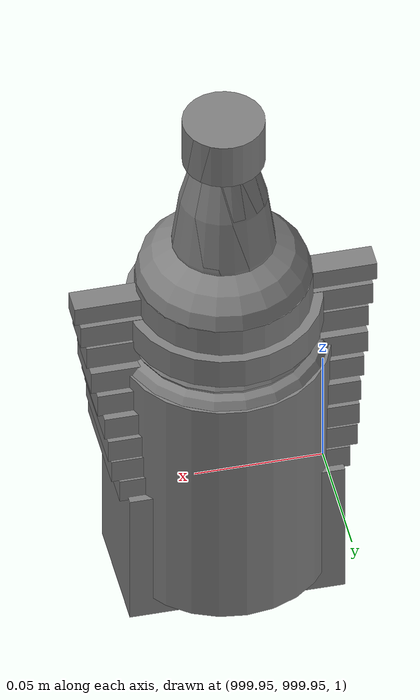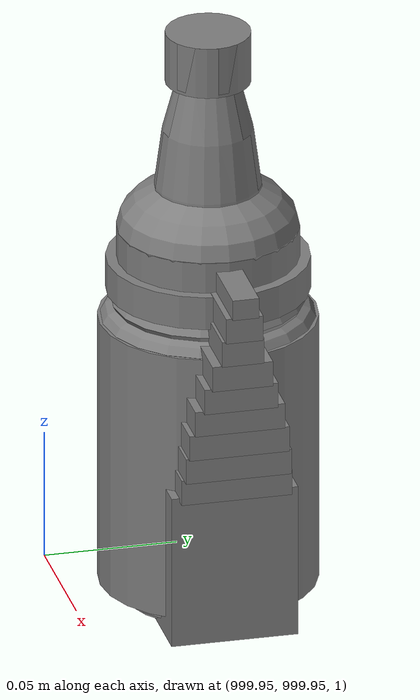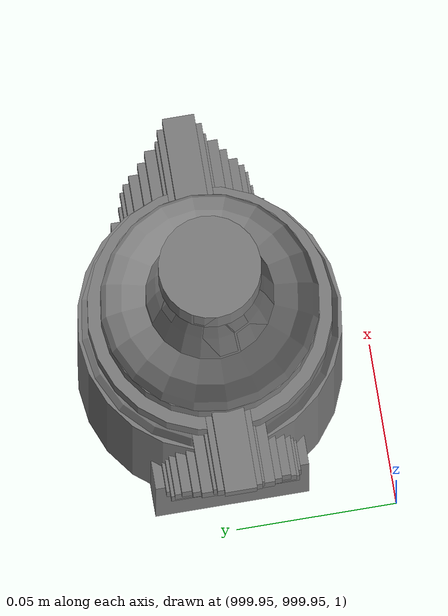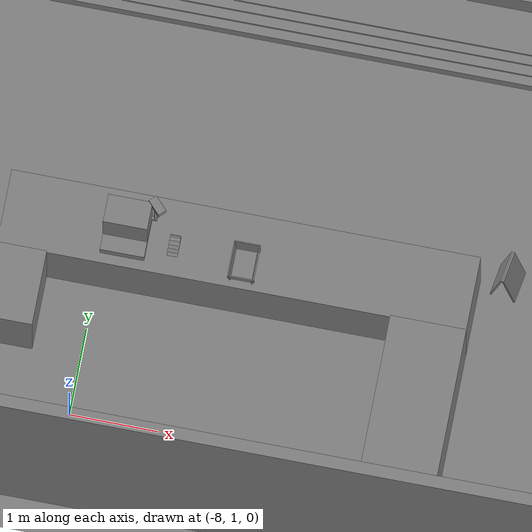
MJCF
<mujoco>
    <option gravity="0.000000000 0.000000000 -9.810000420" timestep="0.0166666" integrator="implicitfast" density="1.225" viscosity="1.8000001e-05" noslip_iterations="10" iterations="100" sdf_iterations="50">
        <flag multiccd="disable"/>
    </option>
    <size memory="1000M"/>
    <compiler coordinate="local"/>
    <worldbody>
        <light cutoff="30" pos="0 1 1" dir="0 -1 -2"/>
        <light cutoff="30" pos="0 -1 1" dir="0 1 -2"/>
        <body pos="-7.168000221 2.823999882 1.227496982" euler="-0.283413976 0.056829724 -0.133293271" name="openloong_gripper_2f85_fix_base_usda_Pos">
            <geom contype="1" conaffinity="1" density="1000" type="box" material="" rgba="0.500000000 0.500000000 0.500000000 1.000000000" solimp="0.899999976 0.949999988 0.001000000" friction="1.000000000 0.005000000 0.000100000" solref="0.020000000 1.000000000" margin="0" condim="3" group="0" pos="-0.002278805 0.074524641 -0.004134059" quat="0.315989345 0.948763072 -0.000000000 0.000000000" size="0.059999999 0.013000000 0.035000000" name="openloong_gripper_2f85_fix_base_usda_geom_C591AA49_1DB0_4505_AA96_FFF1210115FD"/>
            <geom contype="1" conaffinity="1" density="1000" type="box" material="" rgba="0.500000000 0.500000000 0.500000000 1.000000000" solimp="0.899999976 0.949999988 0.001000000" friction="1.000000000 0.005000000 0.000100000" solref="0.020000000 1.000000000" margin="0" condim="3" group="0" pos="-0.002278805 0.078031301 0.008128285" quat="0.990447521 -0.137893379 -0.000000000 -0.000000000" size="0.059999999 0.010000000 0.035000000" name="openloong_gripper_2f85_fix_base_usda_geom_D1B6ED51_F35B_4FFE_A9B8_279257F1F48A"/>
            <geom contype="1" conaffinity="1" density="1000" type="box" material="" rgba="0.500000000 0.500000000 0.500000000 1.000000000" solimp="0.899999976 0.949999988 0.001000000" friction="1.000000000 0.005000000 0.000100000" solref="0.020000000 1.000000000" margin="0" condim="3" group="0" pos="-0.002278805 0.080785275 -0.002596974" quat="0.287325472 -0.957833409 0.000000000 -0.000000000" size="0.059999999 0.013000000 0.035000000" name="openloong_gripper_2f85_fix_base_usda_geom_034B7AEF_0654_406A_92CA_541E3D9B48BE"/>
            <geom contype="1" conaffinity="1" density="1000" type="box" material="" rgba="0.500000000 0.500000000 0.500000000 1.000000000" solimp="0.899999976 0.949999988 0.001000000" friction="1.000000000 0.005000000 0.000100000" solref="0.020000000 1.000000000" margin="0" condim="3" group="0" pos="-0.002278805 -0.098804474 -0.020146966" quat="0.988851666 0.148906454 0.000000000 -0.000000000" size="0.059999999 0.022000000 0.020000000" name="openloong_gripper_2f85_fix_base_usda_geom_531AF713_92D0_47C1_A269_E2B0AC2072C1"/>
            <geom contype="1" conaffinity="1" density="1000" type="box" material="" rgba="0.500000000 0.500000000 0.500000000 1.000000000" solimp="0.899999976 0.949999988 0.001000000" friction="1.000000000 0.005000000 0.000100000" solref="0.020000000 1.000000000" margin="0" condim="3" group="0" pos="-0.002279282 0.019920111 0.012102962" quat="0.995421767 0.095583342 -0.000000000 -0.000000000" size="0.059999999 0.025000000 0.026000001" name="openloong_gripper_2f85_fix_base_usda_geom_AFF17600_5890_4A8E_A90E_019040EB081B"/>
            <geom contype="1" conaffinity="1" density="1000" type="box" material="" rgba="0.500000000 0.500000000 0.500000000 1.000000000" solimp="0.899999976 0.949999988 0.001000000" friction="1.000000000 0.005000000 0.000100000" solref="0.020000000 1.000000000" margin="0" condim="3" group="0" pos="-0.002279282 0.005734444 -0.014276862" quat="0.999571741 -0.029275302 -0.000000000 -0.000000000" size="0.059999999 0.050000001 0.010000000" name="openloong_gripper_2f85_fix_base_usda_geom_3ADCFD2A_1933_4B23_AF00_14B907B0FACB"/>
            <geom contype="1" conaffinity="1" density="1000" type="box" material="" rgba="0.500000000 0.500000000 0.500000000 1.000000000" solimp="0.899999976 0.949999988 0.001000000" friction="1.000000000 0.005000000 0.000100000" solref="0.020000000 1.000000000" margin="0" condim="3" group="0" pos="-0.002278805 0.079460382 0.007771969" quat="0.922590554 -0.385781586 0.000000000 -0.000000000" size="0.059999999 0.010000000 0.035000000" name="openloong_gripper_2f85_fix_base_usda_geom_56192F56_5396_4875_ADFD_79D252F6A1F0"/>
            <geom contype="1" conaffinity="1" density="1000" type="box" material="" rgba="0.500000000 0.500000000 0.500000000 1.000000000" solimp="0.899999976 0.949999988 0.001000000" friction="1.000000000 0.005000000 0.000100000" solref="0.020000000 1.000000000" margin="0" condim="3" group="0" pos="-0.002279282 0.081384182 -0.001320124" quat="0.590483785 -0.807049930 0.000000000 -0.000000000" size="0.059999999 0.013000000 0.035000000" name="openloong_gripper_2f85_fix_base_usda_geom_143D6113_B262_4EC8_B1F2_682EF05D2506"/>
            <geom contype="1" conaffinity="1" density="1000" type="box" material="" rgba="0.500000000 0.500000000 0.500000000 1.000000000" solimp="0.899999976 0.949999988 0.001000000" friction="1.000000000 0.005000000 0.000100000" solref="0.020000000 1.000000000" margin="0" condim="3" group="0" pos="-0.002278805 -0.059297800 -0.007972836" quat="0.988851666 0.148906454 0.000000000 -0.000000000" size="0.059999999 0.020000000 0.022000000" name="openloong_gripper_2f85_fix_base_usda_geom_BA6C0A4C_EA49_46ED_AEF3_63F43A5C3CE7"/>
            <geom contype="1" conaffinity="1" density="1000" type="box" material="" rgba="0.500000000 0.500000000 0.500000000 1.000000000" solimp="0.899999976 0.949999988 0.001000000" friction="1.000000000 0.005000000 0.000100000" solref="0.020000000 1.000000000" margin="0" condim="3" group="0" pos="-0.002278805 0.076618671 -0.004656792" quat="0.004634961 0.999989629 -0.000000000 0.000000000" size="0.059999999 0.013000000 0.035000000" name="openloong_gripper_2f85_fix_base_usda_geom_A05EAD28_6EC8_4540_AB60_835051255796"/>
            <geom contype="1" conaffinity="1" density="1000" type="box" material="" rgba="0.500000000 0.500000000 0.500000000 1.000000000" solimp="0.899999976 0.949999988 0.001000000" friction="1.000000000 0.005000000 0.000100000" solref="0.020000000 1.000000000" margin="0" condim="3" group="0" pos="-0.002279282 -0.021952629 0.002960086" quat="0.991270423 0.131847665 -0.000000000 0.000000000" size="0.059999999 0.020000000 0.024000000" name="openloong_gripper_2f85_fix_base_usda_geom_BDF6493F_DC91_4011_995F_033DB723DD0A"/>
            <geom contype="1" conaffinity="1" density="1000" type="box" material="" rgba="0.500000000 0.500000000 0.500000000 1.000000000" solimp="0.899999976 0.949999988 0.001000000" friction="1.000000000 0.005000000 0.000100000" solref="0.020000000 1.000000000" margin="0" condim="3" group="0" pos="-0.002278805 0.081418991 0.002587914" quat="0.803492308 -0.595315695 0.000000000 -0.000000000" size="0.059999999 0.013000000 0.035000000" name="openloong_gripper_2f85_fix_base_usda_geom_7194AD3F_D8D2_40F5_B4BF_0BEE12C9D701"/>
            <geom contype="1" conaffinity="1" density="1000" type="box" material="" rgba="0.500000000 0.500000000 0.500000000 1.000000000" solimp="0.899999976 0.949999988 0.001000000" friction="1.000000000 0.005000000 0.000100000" solref="0.020000000 1.000000000" margin="0" condim="3" group="0" pos="-0.002278805 0.061115503 0.008545756" quat="0.999326169 0.036714450 0.000000000 -0.000000000" size="0.059999999 0.020000000 0.035000000" name="openloong_gripper_2f85_fix_base_usda_geom_2A9477B7_ED79_471F_A822_4217A54B892C"/>
            <freejoint name="openloong_gripper_2f85_fix_base_usda_pos_scan"/>
        </body>
        <body pos="-2.009059906 6.114023209 1.670913219" euler="-65.807212830 62.318016052 175.691833496" mocap="true" name="spotlight4_SpotLight"/>
        <body pos="1000.000000000 1000.000000000 1.000000000" euler="0.000000000 0.000000000 0.000000000" name="openloong_gripper_2f85_fix_base_usda_bottle_red">
            <geom contype="1" conaffinity="1" density="1000" type="ellipsoid" material="" rgba="0.500000000 0.500000000 0.500000000 1.000000000" solimp="0.899999976 0.949999988 0.001000000" friction="1.000000000 0.005000000 0.000100000" solref="0.020000000 1.000000000" margin="0" condim="3" group="0" pos="0.000000000 0.000000000 0.144284487" quat="1.000000000 0.000000000 0.000000000 0.000000000" size="0.021000000 0.021000000 0.079999998" name="openloong_gripper_2f85_fix_base_usda_geom_049210DA_BC39_49A7_B714_99AF1ACC27A5"/>
            <geom contype="1" conaffinity="1" density="1000" type="cylinder" material="" rgba="0.500000000 0.500000000 0.500000000 1.000000000" solimp="0.899999976 0.949999988 0.001000000" friction="1.000000000 0.005000000 0.000100000" solref="0.020000000 1.000000000" margin="0" condim="3" group="0" pos="0.000000000 0.000000000 0.220618963" quat="1.000000000 0.000000000 0.000000000 0.000000000" size="0.016000001 0.010000000 1.000000000" name="openloong_gripper_2f85_fix_base_usda_geom_55E23BEE_7106_4A72_8694_C5403007ABF6"/>
            <geom contype="1" conaffinity="1" density="1000" type="ellipsoid" material="" rgba="0.500000000 0.500000000 0.500000000 1.000000000" solimp="0.899999976 0.949999988 0.001000000" friction="1.000000000 0.005000000 0.000100000" solref="0.020000000 1.000000000" margin="0" condim="3" group="0" pos="0.000000000 0.000000000 0.118945479" quat="1.000000000 0.000000000 0.000000000 0.000000000" size="0.030999999 0.030999999 0.029999999" name="openloong_gripper_2f85_fix_base_usda_geom_6C93F613_7E75_42F5_BD26_E28FD1117A4F"/>
            <geom contype="1" conaffinity="1" density="1000" type="box" material="" rgba="0.500000000 0.500000000 0.500000000 1.000000000" solimp="0.899999976 0.949999988 0.001000000" friction="1.000000000 0.005000000 0.000100000" solref="0.020000000 1.000000000" margin="0" condim="3" group="0" pos="0.000000000 0.000000000 0.002189159" quat="1.000000000 0.000000000 0.000000000 0.000000000" size="0.020000000 0.020000000 0.003000000" name="openloong_gripper_2f85_fix_base_usda_geom_6B84E901_C25A_4CC8_8F29_982C621F9CD0"/>
            <geom contype="1" conaffinity="1" density="1000" type="cylinder" material="" rgba="0.500000000 0.500000000 0.500000000 1.000000000" solimp="0.899999976 0.949999988 0.001000000" friction="1.000000000 0.005000000 0.000100000" solref="0.020000000 1.000000000" margin="0" condim="3" group="0" pos="0.000000000 -0.000366211 0.060884237" quat="1.000000000 0.000000000 0.000000000 0.000000000" size="0.030999999 0.057999998 1.000000000" name="openloong_gripper_2f85_fix_base_usda_geom_06DAFEDA_6CBC_46C3_A858_50EC1363ABBD"/>
            <freejoint name="openloong_gripper_2f85_fix_base_usda_bottle_red_joint"/>
            <site size="0.005000000 0.005000000 0.005000000" rgba="0.500000000 0.500000000 0.500000000 1.000000000" pos="0.000000000 0.000000000 0.000000000" quat="0.999961913 0.008726535 0.000000000 0.000000000" group="0" type="sphere" name="openloong_gripper_2f85_fix_base_usda_bottle_redsite"/>
        </body>
        <body pos="1000.000000000 1000.000000000 1.000000000" euler="0.000000000 0.000000000 0.000000000" name="openloong_gripper_2f85_fix_base_usda_can">
            <geom contype="1" conaffinity="1" density="1000" type="cylinder" material="" rgba="0.500000000 0.500000000 0.500000000 1.000000000" solimp="0.899999976 0.949999988 0.001000000" friction="1.000000000 0.005000000 0.000100000" solref="0.020000000 1.000000000" margin="0" condim="3" group="0" pos="0.000000000 0.000000000 0.079676986" quat="1.000000000 0.000000000 0.000000000 0.000000000" size="0.034000002 0.071999997 1.000000000" name="openloong_gripper_2f85_fix_base_usda_geom_4CB0BCC7_DBCB_490B_A6C6_8F050B0666C2"/>
            <geom contype="1" conaffinity="1" density="1000" type="ellipsoid" material="" rgba="0.500000000 0.500000000 0.500000000 1.000000000" solimp="0.899999976 0.949999988 0.001000000" friction="1.000000000 0.005000000 0.000100000" solref="0.020000000 1.000000000" margin="0" condim="3" group="0" pos="0.000000000 0.000000000 0.151854277" quat="1.000000000 0.000000000 0.000000000 0.000000000" size="0.034000002 0.034000002 0.020000000" name="openloong_gripper_2f85_fix_base_usda_geom_80F3520D_9BCE_42BF_B4A3_65BE358304E0"/>
            <geom contype="1" conaffinity="1" density="1000" type="box" material="" rgba="0.500000000 0.500000000 0.500000000 1.000000000" solimp="0.899999976 0.949999988 0.001000000" friction="1.000000000 0.005000000 0.000100000" solref="0.020000000 1.000000000" margin="0" condim="3" group="0" pos="0.000000000 0.000000000 0.004777670" quat="1.000000000 0.000000000 0.000000000 0.000000000" size="0.020000000 0.020000000 0.005000000" name="openloong_gripper_2f85_fix_base_usda_geom_003B2C30_D580_4965_93D8_61FCA728E16D"/>
            <freejoint name="openloong_gripper_2f85_fix_base_usda_can_joint"/>
            <site size="0.005000000 0.005000000 0.005000000" rgba="0.500000000 0.500000000 0.500000000 1.000000000" pos="0.000000000 0.000000000 0.000000000" quat="1.000000000 0.000000000 0.000000000 0.000000000" group="0" type="sphere" name="openloong_gripper_2f85_fix_base_usda_cansite"/>
        </body>
        <body pos="1000.000000000 1000.000000000 1.000000000" euler="0.000000000 0.000000000 0.000000000" name="openloong_gripper_2f85_fix_base_usda_jar_01">
            <geom contype="1" conaffinity="1" density="1000" type="box" material="" rgba="0.500000000 0.500000000 0.500000000 1.000000000" solimp="0.899999976 0.949999988 0.001000000" friction="1.000000000 0.005000000 0.000100000" solref="0.020000000 1.000000000" margin="0" condim="3" group="0" pos="0.000000000 0.000000000 0.006158113" quat="1.000000000 0.000000000 0.000000000 0.000000000" size="0.020000000 0.020000000 0.005000000" name="openloong_gripper_2f85_fix_base_usda_geom_A8485F0A_C470_4F5A_A336_3DC14E9A1E13"/>
            <geom contype="1" conaffinity="1" density="1000" type="cylinder" material="" rgba="0.500000000 0.500000000 0.500000000 1.000000000" solimp="0.899999976 0.949999988 0.001000000" friction="1.000000000 0.005000000 0.000100000" solref="0.020000000 1.000000000" margin="0" condim="3" group="0" pos="0.000000000 0.000000000 0.062744498" quat="1.000000000 0.000000000 0.000000000 0.000000000" size="0.041000001 0.052999999 1.000000000" name="openloong_gripper_2f85_fix_base_usda_geom_856BF834_6E1B_45B0_AED7_870000EF56F8"/>
            <geom contype="1" conaffinity="1" density="1000" type="ellipsoid" material="" rgba="0.500000000 0.500000000 0.500000000 1.000000000" solimp="0.899999976 0.949999988 0.001000000" friction="1.000000000 0.005000000 0.000100000" solref="0.020000000 1.000000000" margin="0" condim="3" group="0" pos="0.000000000 0.000000000 0.122252703" quat="1.000000000 0.000000000 0.000000000 0.000000000" size="0.035999998 0.035999998 0.010000000" name="openloong_gripper_2f85_fix_base_usda_geom_8DD764DA_FDCA_4E4C_86AB_D340BC5B177A"/>
            <geom contype="1" conaffinity="1" density="1000" type="cylinder" material="" rgba="0.500000000 0.500000000 0.500000000 1.000000000" solimp="0.899999976 0.949999988 0.001000000" friction="1.000000000 0.005000000 0.000100000" solref="0.020000000 1.000000000" margin="0" condim="3" group="0" pos="0.000000000 0.000000000 0.015747190" quat="1.000000000 0.000000000 0.000000000 0.000000000" size="0.035000000 0.010000000 1.000000000" name="openloong_gripper_2f85_fix_base_usda_geom_ECEF071E_0E2D_4914_918F_91518E614076"/>
            <geom contype="1" conaffinity="1" density="1000" type="ellipsoid" material="" rgba="0.500000000 0.500000000 0.500000000 1.000000000" solimp="0.899999976 0.949999988 0.001000000" friction="1.000000000 0.005000000 0.000100000" solref="0.020000000 1.000000000" margin="0" condim="3" group="0" pos="0.000000000 0.000000000 0.115815401" quat="1.000000000 0.000000000 0.000000000 0.000000000" size="0.039999999 0.039999999 0.010000000" name="openloong_gripper_2f85_fix_base_usda_geom_9A277C4D_30DC_42C5_964F_0ECC278540DD"/>
            <geom contype="1" conaffinity="1" density="1000" type="cylinder" material="" rgba="0.500000000 0.500000000 0.500000000 1.000000000" solimp="0.899999976 0.949999988 0.001000000" friction="1.000000000 0.005000000 0.000100000" solref="0.020000000 1.000000000" margin="0" condim="3" group="0" pos="0.000000000 0.000000000 0.133183479" quat="1.000000000 0.000000000 0.000000000 0.000000000" size="0.037999999 0.006500000 1.000000000" name="openloong_gripper_2f85_fix_base_usda_geom_70264D7C_77EF_4917_BA5E_9EF2FF16DC11"/>
            <freejoint name="openloong_gripper_2f85_fix_base_usda_jar_01_joint"/>
            <site size="0.005000000 0.005000000 0.005000000" rgba="0.500000000 0.500000000 0.500000000 1.000000000" pos="0.000000000 0.000000000 0.000000000" quat="1.000000000 0.000000000 0.000000000 0.000000000" group="0" type="sphere" name="openloong_gripper_2f85_fix_base_usda_jar_01site"/>
        </body>
        <body pos="-1.950639844 5.852279663 1.765811563" euler="4.413654804 48.378368378 149.717651367" mocap="true" name="spotlight1_SpotLight"/>
        <body pos="1000.000000000 1000.000000000 1.000000000" euler="0.000000000 0.000000000 0.000000000" name="openloong_gripper_2f85_fix_base_usda_bottle_blue">
            <geom contype="1" conaffinity="1" density="1000" type="ellipsoid" material="" rgba="0.500000000 0.500000000 0.500000000 1.000000000" solimp="0.899999976 0.949999988 0.001000000" friction="1.000000000 0.005000000 0.000100000" solref="0.020000000 1.000000000" margin="0" condim="3" group="0" pos="0.000000000 0.000000000 0.118920922" quat="1.000000000 0.000000000 0.000000000 0.000000000" size="0.030999999 0.030999999 0.029999999" name="openloong_gripper_2f85_fix_base_usda_geom_3CD3CF2E_EA1A_4494_8B33_39A472720899"/>
            <geom contype="1" conaffinity="1" density="1000" type="box" material="" rgba="0.500000000 0.500000000 0.500000000 1.000000000" solimp="0.899999976 0.949999988 0.001000000" friction="1.000000000 0.005000000 0.000100000" solref="0.020000000 1.000000000" margin="0" condim="3" group="0" pos="0.000000000 0.000000000 0.002164602" quat="1.000000000 0.000000000 0.000000000 0.000000000" size="0.020000000 0.020000000 0.003000000" name="openloong_gripper_2f85_fix_base_usda_geom_1DD5D268_3EAB_45A7_9AE3_672C7B90F91E"/>
            <geom contype="1" conaffinity="1" density="1000" type="cylinder" material="" rgba="0.500000000 0.500000000 0.500000000 1.000000000" solimp="0.899999976 0.949999988 0.001000000" friction="1.000000000 0.005000000 0.000100000" solref="0.020000000 1.000000000" margin="0" condim="3" group="0" pos="0.000000000 -0.000366211 0.060859680" quat="1.000000000 0.000000000 0.000000000 0.000000000" size="0.030999999 0.057999998 1.000000000" name="openloong_gripper_2f85_fix_base_usda_geom_BC9329F0_7375_4B9B_9CD2_7ECBBBBB0B0F"/>
            <geom contype="1" conaffinity="1" density="1000" type="cylinder" material="" rgba="0.500000000 0.500000000 0.500000000 1.000000000" solimp="0.899999976 0.949999988 0.001000000" friction="1.000000000 0.005000000 0.000100000" solref="0.020000000 1.000000000" margin="0" condim="3" group="0" pos="0.000000000 0.000000000 0.220594406" quat="1.000000000 0.000000000 0.000000000 0.000000000" size="0.016000001 0.010000000 1.000000000" name="openloong_gripper_2f85_fix_base_usda_geom_24A1EFC8_3C56_42F2_9490_F3C1F819AAC8"/>
            <geom contype="1" conaffinity="1" density="1000" type="ellipsoid" material="" rgba="0.500000000 0.500000000 0.500000000 1.000000000" solimp="0.899999976 0.949999988 0.001000000" friction="1.000000000 0.005000000 0.000100000" solref="0.020000000 1.000000000" margin="0" condim="3" group="0" pos="0.000000000 0.000000000 0.144259930" quat="1.000000000 0.000000000 0.000000000 0.000000000" size="0.021000000 0.021000000 0.079999998" name="openloong_gripper_2f85_fix_base_usda_geom_8B68D7EF_D475_45BE_80D9_C58576B7DD59"/>
            <freejoint name="openloong_gripper_2f85_fix_base_usda_bottle_blue_joint"/>
            <site size="0.005000000 0.005000000 0.005000000" rgba="0.500000000 0.500000000 0.500000000 1.000000000" pos="0.000000000 0.000000000 0.000000000" quat="0.999961913 0.008726535 0.000000000 0.000000000" group="0" type="sphere" name="openloong_gripper_2f85_fix_base_usda_bottle_bluesite"/>
        </body>
        <body pos="1000.000000000 1000.000000000 1.000000000" euler="0.000000000 0.000000000 0.000000000" name="openloong_gripper_2f85_fix_base_usda_salt">
            <geom contype="1" conaffinity="1" density="1000" type="box" material="" rgba="0.500000000 0.500000000 0.500000000 1.000000000" solimp="0.899999976 0.949999988 0.001000000" friction="1.000000000 0.005000000 0.000100000" solref="0.020000000 1.000000000" margin="0" condim="3" group="0" pos="0.000305176 0.000000000 0.084862232" quat="1.000000000 0.000000000 0.000000000 0.000000000" size="0.048999999 0.018999999 0.005000000" name="openloong_gripper_2f85_fix_base_usda_geom_33034FFE_7D21_4393_9CB1_6AC15A055F8B"/>
            <geom contype="1" conaffinity="1" density="1000" type="box" material="" rgba="0.500000000 0.500000000 0.500000000 1.000000000" solimp="0.899999976 0.949999988 0.001000000" friction="1.000000000 0.005000000 0.000100000" solref="0.020000000 1.000000000" margin="0" condim="3" group="0" pos="0.000305176 0.000000000 0.104564309" quat="1.000000000 0.000000000 0.000000000 0.000000000" size="0.052000001 0.014000000 0.005000000" name="openloong_gripper_2f85_fix_base_usda_geom_C8F12BFC_3709_4BFE_B4D3_03363826816F"/>
            <geom contype="1" conaffinity="1" density="1000" type="box" material="" rgba="0.500000000 0.500000000 0.500000000 1.000000000" solimp="0.899999976 0.949999988 0.001000000" friction="1.000000000 0.005000000 0.000100000" solref="0.020000000 1.000000000" margin="0" condim="3" group="0" pos="0.000305176 0.000000000 0.114487171" quat="1.000000000 0.000000000 0.000000000 0.000000000" size="0.054000001 0.011500000 0.005000000" name="openloong_gripper_2f85_fix_base_usda_geom_B7C714AC_D304_45C4_82B1_1C03FC05C006"/>
            <geom contype="1" conaffinity="1" density="1000" type="box" material="" rgba="0.500000000 0.500000000 0.500000000 1.000000000" solimp="0.899999976 0.949999988 0.001000000" friction="1.000000000 0.005000000 0.000100000" solref="0.020000000 1.000000000" margin="0" condim="3" group="0" pos="0.000305176 0.000000000 0.075103164" quat="1.000000000 0.000000000 0.000000000 0.000000000" size="0.048000000 0.020000000 0.005000000" name="openloong_gripper_2f85_fix_base_usda_geom_88749516_646A_47F7_BE9D_EFA905BB9035"/>
            <geom contype="1" conaffinity="1" density="1000" type="box" material="" rgba="0.500000000 0.500000000 0.500000000 1.000000000" solimp="0.899999976 0.949999988 0.001000000" friction="1.000000000 0.005000000 0.000100000" solref="0.020000000 1.000000000" margin="0" condim="3" group="0" pos="0.000305176 0.000000000 0.134892464" quat="1.000000000 0.000000000 0.000000000 0.000000000" size="0.057000000 0.007000000 0.005000000" name="openloong_gripper_2f85_fix_base_usda_geom_7C2627CC_5BE8_4385_8F62_9DE3CFB002F5"/>
            <geom contype="1" conaffinity="1" density="1000" type="box" material="" rgba="0.500000000 0.500000000 0.500000000 1.000000000" solimp="0.899999976 0.949999988 0.001000000" friction="1.000000000 0.005000000 0.000100000" solref="0.020000000 1.000000000" margin="0" condim="3" group="0" pos="0.000305176 0.000000000 0.094920278" quat="1.000000000 0.000000000 0.000000000 0.000000000" size="0.050000001 0.017000001 0.005000000" name="openloong_gripper_2f85_fix_base_usda_geom_637EEDEB_74B3_4E16_9A52_AB1384AE3E8F"/>
            <geom contype="1" conaffinity="1" density="1000" type="box" material="" rgba="0.500000000 0.500000000 0.500000000 1.000000000" solimp="0.899999976 0.949999988 0.001000000" friction="1.000000000 0.005000000 0.000100000" solref="0.020000000 1.000000000" margin="0" condim="3" group="0" pos="0.000305176 0.000000000 0.065204859" quat="1.000000000 0.000000000 0.000000000 0.000000000" size="0.045000002 0.021000000 0.005000000" name="openloong_gripper_2f85_fix_base_usda_geom_B6343AF8_C252_4CC9_8BE9_1374443FB2EF"/>
            <geom contype="1" conaffinity="1" density="1000" type="box" material="" rgba="0.500000000 0.500000000 0.500000000 1.000000000" solimp="0.899999976 0.949999988 0.001000000" friction="1.000000000 0.005000000 0.000100000" solref="0.020000000 1.000000000" margin="0" condim="3" group="0" pos="0.000305176 0.000000000 0.144135714" quat="1.000000000 0.000000000 0.000000000 0.000000000" size="0.059000000 0.005000000 0.004000000" name="openloong_gripper_2f85_fix_base_usda_geom_CB9049E4_DFA7_4A66_B0C1_070864129FC8"/>
            <geom contype="1" conaffinity="1" density="1000" type="box" material="" rgba="0.500000000 0.500000000 0.500000000 1.000000000" solimp="0.899999976 0.949999988 0.001000000" friction="1.000000000 0.005000000 0.000100000" solref="0.020000000 1.000000000" margin="0" condim="3" group="0" pos="0.000000000 0.000000000 0.031593561" quat="1.000000000 0.000000000 0.000000000 0.000000000" size="0.041999999 0.024000000 0.029999999" name="openloong_gripper_2f85_fix_base_usda_geom_3E7F7443_BDA5_4044_93FA_565CC4993480"/>
            <geom contype="1" conaffinity="1" density="1000" type="box" material="" rgba="0.500000000 0.500000000 0.500000000 1.000000000" solimp="0.899999976 0.949999988 0.001000000" friction="1.000000000 0.005000000 0.000100000" solref="0.020000000 1.000000000" margin="0" condim="3" group="0" pos="0.000305176 0.000000000 0.124608755" quat="1.000000000 0.000000000 0.000000000 0.000000000" size="0.055000000 0.008000000 0.005000000" name="openloong_gripper_2f85_fix_base_usda_geom_F9ED1AAC_BEDC_4071_B071_2A4E8FDFA5A4"/>
            <freejoint name="openloong_gripper_2f85_fix_base_usda_salt_joint"/>
            <site size="0.005000000 0.005000000 0.005000000" rgba="0.500000000 0.500000000 0.500000000 1.000000000" pos="0.000000000 0.000000000 0.000000000" quat="1.000000000 0.000000000 0.000000000 0.000000000" group="0" type="sphere" name="openloong_gripper_2f85_fix_base_usda_saltsite"/>
        </body>
        <body pos="-1.819503307 6.341538906 1.835785151" euler="-72.251197815 -52.531455994 -153.827087402" mocap="true" name="spotlight6_SpotLight"/>
        <body pos="0.000000000 0.000000000 0.000000000" euler="0.000000000 0.000000000 0.000000000" name="Interactive Objects_Interactive Objects"/>
        <body pos="0.000000000 0.000000000 0.000000000" euler="0.000000000 0.000000000 0.000000000" name=" Static Objects_ Static Objects">
            <geom contype="1" conaffinity="1" density="1000" type="box" material="" rgba="0.500000000 0.500000000 0.500000000 1.000000000" solimp="0.899999976 0.949999988 0.001000000" friction="1.000000000 0.005000000 0.000100000" solref="0.020000000 1.000000000" margin="0" condim="3" group="0" pos="-6.286010742 6.153595448 1.563861728" quat="0.707107067 0.000000000 0.000000000 0.707106471" size="0.529999971 3.134999990 0.025000000" name=" Static Objects_geom_08B1D773_DB59_4EC7_8BEA_685E8E5745C8"/>
            <geom contype="1" conaffinity="1" density="1000" type="box" material="" rgba="0.500000000 0.500000000 0.500000000 1.000000000" solimp="0.899999976 0.949999988 0.001000000" friction="1.000000000 0.005000000 0.000100000" solref="0.020000000 1.000000000" margin="0" condim="3" group="0" pos="-3.101639986 6.150595188 1.018643856" quat="1.000000000 0.000000000 0.000000000 0.000000000" size="0.050000001 0.579999983 1.019999981" name=" Static Objects_geom_812A21A9_2B12_43E9_9A58_80EE0C8BCA38"/>
            <geom contype="1" conaffinity="1" density="1000" type="box" material="" rgba="0.500000000 0.500000000 0.500000000 1.000000000" solimp="0.899999976 0.949999988 0.001000000" friction="1.000000000 0.005000000 0.000100000" solref="0.020000000 1.000000000" margin="0" condim="3" group="0" pos="-2.825197220 6.153595448 1.563861728" quat="0.707107067 0.000000000 0.000000000 0.707106471" size="0.550000012 0.239999995 0.025000000" name=" Static Objects_geom_D7087897_E14F_48B4_9F73_3DACBE36ADAD"/>
            <geom contype="1" conaffinity="1" density="1000" type="box" material="" rgba="0.500000000 0.500000000 0.500000000 1.000000000" solimp="0.899999976 0.949999988 0.001000000" friction="1.000000000 0.005000000 0.000100000" solref="0.020000000 1.000000000" margin="0" condim="3" group="0" pos="-6.311686516 6.153595448 1.018643856" quat="0.707107067 0.000000000 0.000000000 0.707106471" size="0.050000001 3.150000095 1.019999981" name=" Static Objects_geom_A0AC539A_30E2_4BDD_A916_5B102551F779"/>
            <geom contype="1" conaffinity="1" density="1000" type="box" material="" rgba="0.500000000 0.500000000 0.500000000 1.000000000" solimp="0.899999976 0.949999988 0.001000000" friction="1.000000000 0.005000000 0.000100000" solref="0.020000000 1.000000000" margin="0" condim="3" group="0" pos="-2.825197220 6.153595448 1.115278244" quat="0.707107067 0.000000000 0.000000000 0.707106471" size="0.550000012 0.239999995 0.025000000" name=" Static Objects_geom_B5EDC3F7_0EDB_4E8B_AE7B_F265D7CE842E"/>
            <geom contype="1" conaffinity="1" density="1000" type="box" material="" rgba="0.500000000 0.500000000 0.500000000 1.000000000" solimp="0.899999976 0.949999988 0.001000000" friction="1.000000000 0.005000000 0.000100000" solref="0.020000000 1.000000000" margin="0" condim="3" group="0" pos="-6.293097973 6.153595448 1.114443064" quat="0.707107067 0.000000000 0.000000000 0.707106471" size="0.529999971 3.134999990 0.025000000" name=" Static Objects_geom_6BB9B888_D531_4973_BE8F_EA9D6A259BE6"/>
            <geom contype="1" conaffinity="1" density="1000" type="box" material="" rgba="0.500000000 0.500000000 0.500000000 1.000000000" solimp="0.899999976 0.949999988 0.001000000" friction="1.000000000 0.005000000 0.000100000" solref="0.020000000 1.000000000" margin="0" condim="3" group="0" pos="-2.825197220 6.153595448 0.629031777" quat="0.707107067 0.000000000 0.000000000 0.707106471" size="0.550000012 0.239999995 0.025000000" name=" Static Objects_geom_7F4EE7E9_EE40_4CEE_9FF4_CD130C94BE8F"/>
            <geom contype="1" conaffinity="1" density="1000" type="box" material="" rgba="0.500000000 0.500000000 0.500000000 1.000000000" solimp="0.899999976 0.949999988 0.001000000" friction="1.000000000 0.005000000 0.000100000" solref="0.020000000 1.000000000" margin="0" condim="3" group="0" pos="-6.286010742 6.153595448 0.096129179" quat="0.707107067 0.000000000 0.000000000 0.707106471" size="0.529999971 3.134999990 0.098999999" name=" Static Objects_geom_DEDE4707_B814_4F3A_8A70_35A010B694B3"/>
            <geom contype="1" conaffinity="1" density="1000" type="box" material="" rgba="0.500000000 0.500000000 0.500000000 1.000000000" solimp="0.899999976 0.949999988 0.001000000" friction="1.000000000 0.005000000 0.000100000" solref="0.020000000 1.000000000" margin="0" condim="3" group="0" pos="-2.825197220 6.153595448 0.097434282" quat="0.707107067 0.000000000 0.000000000 0.707106471" size="0.550000012 0.239999995 0.098999999" name=" Static Objects_geom_88471213_E4C2_40AB_BABF_6F33EE653025"/>
            <geom contype="1" conaffinity="1" density="1000" type="box" material="" rgba="0.500000000 0.500000000 0.500000000 1.000000000" solimp="0.899999976 0.949999988 0.001000000" friction="1.000000000 0.005000000 0.000100000" solref="0.020000000 1.000000000" margin="0" condim="3" group="0" pos="-6.286010742 6.153595448 0.629031777" quat="0.707107067 0.000000000 0.000000000 0.707106471" size="0.529999971 3.134999990 0.025000000" name=" Static Objects_geom_837D62FC_455B_4D6E_9AFB_27E205FB5A10"/>
            <geom contype="1" conaffinity="1" density="1000" type="box" material="" rgba="0.500000000 0.500000000 0.500000000 1.000000000" solimp="0.899999976 0.949999988 0.001000000" friction="1.000000000 0.005000000 0.000100000" solref="0.020000000 1.000000000" margin="0" condim="3" group="0" pos="-6.000000000 20.159999847 2.000000000" quat="1.000000000 0.000000000 0.000000000 0.000000000" size="6.079999924 0.070000000 2.000000000" name=" Static Objects_geom_ED05061A_05D2_4E91_8BB5_74296505D2EC"/>
            <geom contype="1" conaffinity="1" density="1000" type="box" material="" rgba="0.500000000 0.500000000 0.500000000 1.000000000" solimp="0.899999976 0.949999988 0.001000000" friction="1.000000000 0.005000000 0.000100000" solref="0.020000000 1.000000000" margin="0" condim="3" group="0" pos="-6.000000000 0.035000000 2.000000000" quat="1.000000000 0.000000000 0.000000000 0.000000000" size="6.079999924 0.070000000 2.000000000" name=" Static Objects_geom_6D96821A_C242_4219_856D_1CEC48F43983"/>
            <geom contype="1" conaffinity="1" density="1000" type="box" material="" rgba="0.500000000 0.500000000 0.500000000 1.000000000" solimp="0.899999976 0.949999988 0.001000000" friction="1.000000000 0.005000000 0.000100000" solref="0.020000000 1.000000000" margin="0" condim="3" group="0" pos="0.000000000 10.000000000 2.000000000" quat="1.000000000 0.000000000 0.000000000 0.000000000" size="0.070000000 10.500000000 2.000000000" name=" Static Objects_geom_44351A99_3C3B_4638_88D9_AF53F3C5A249"/>
            <geom contype="1" conaffinity="1" density="1000" type="box" material="" rgba="0.500000000 0.500000000 0.500000000 1.000000000" solimp="0.899999976 0.949999988 0.001000000" friction="1.000000000 0.005000000 0.000100000" solref="0.020000000 1.000000000" margin="0" condim="3" group="0" pos="-12.050000191 10.000000000 2.000000000" quat="1.000000000 0.000000000 0.000000000 0.000000000" size="0.070000000 10.500000000 2.000000000" name=" Static Objects_geom_57027776_C91B_4D74_91C1_D2EC9AE49CB9"/>
            <geom contype="1" conaffinity="1" density="1000" type="plane" material="" rgba="0.500000000 0.500000000 0.500000000 1.000000000" solimp="0.899999976 0.949999988 0.001000000" friction="1.000000000 0.005000000 0.000100000" solref="0.020000000 1.000000000" margin="0" condim="3" group="0" pos="-6.000000000 10.399999619 0.000000000" quat="1.000000000 0.000000000 0.000000000 0.000000000" size="6.050000191 10.800000191 0.010000000" name=" Static Objects_geom_F27F9531_B8A0_4AC0_BCF4_EAF9923E864B"/>
            <geom contype="1" conaffinity="1" density="1000" type="box" material="" rgba="0.500000000 0.500000000 0.500000000 1.000000000" solimp="0.899999976 0.949999988 0.001000000" friction="1.000000000 0.005000000 0.000100000" solref="0.020000000 1.000000000" margin="0" condim="3" group="0" pos="-8.830721855 2.096410990 0.549305558" quat="1.000000000 0.000000000 0.000000000 0.000000000" size="0.280000001 0.430000007 0.550000012" name=" Static Objects_geom_E6BEBFFB_4EE4_4E32_9A9C_6CC80233C2C1"/>
            <geom contype="1" conaffinity="1" density="1000" type="box" material="" rgba="0.500000000 0.500000000 0.500000000 1.000000000" solimp="0.899999976 0.949999988 0.001000000" friction="1.000000000 0.005000000 0.000100000" solref="0.020000000 1.000000000" margin="0" condim="3" group="0" pos="-6.460197449 2.937205315 0.548931718" quat="1.000000000 0.000000000 0.000000000 0.000000000" size="2.650000095 0.430000007 0.550000012" name=" Static Objects_geom_2F3FEC8B_8203_4D1C_80F5_B4577D094DDD"/>
            <geom contype="1" conaffinity="1" density="1000" type="box" material="" rgba="0.500000000 0.500000000 0.500000000 1.000000000" solimp="0.899999976 0.949999988 0.001000000" friction="1.000000000 0.005000000 0.000100000" solref="0.020000000 1.000000000" margin="0" condim="3" group="0" pos="-4.240264893 1.327049494 0.549888909" quat="1.000000000 0.000000000 0.000000000 0.000000000" size="0.430000007 1.200000048 0.550000012" name=" Static Objects_geom_07013963_B90A_4C24_ADD9_3B9D0C1A0227"/>
            <geom contype="1" conaffinity="1" density="1000" type="box" material="" rgba="0.500000000 0.500000000 0.500000000 1.000000000" solimp="0.899999976 0.949999988 0.001000000" friction="1.000000000 0.005000000 0.000100000" solref="0.020000000 1.000000000" margin="0" condim="3" group="0" pos="-7.408766270 3.088089943 1.776644945" quat="0.928051054 0.000000000 0.000000000 0.372453064" size="0.050000001 0.100000001 0.050000001" name=" Static Objects_geom_540A6AC2_3218_49EA_9722_CB509619B7D7"/>
            <geom contype="1" conaffinity="1" density="1000" type="box" material="" rgba="0.500000000 0.500000000 0.500000000 1.000000000" solimp="0.899999976 0.949999988 0.001000000" friction="1.000000000 0.005000000 0.000100000" solref="0.020000000 1.000000000" margin="0" condim="3" group="0" pos="-7.437745571 3.067511320 1.289965630" quat="1.000000000 0.000000000 0.000000000 0.000000000" size="0.029999999 0.020000000 0.020000000" name=" Static Objects_geom_3A3E3D3F_CF6F_4FC9_9957_278E5423087A"/>
            <geom contype="1" conaffinity="1" density="1000" type="box" material="" rgba="0.500000000 0.500000000 0.500000000 1.000000000" solimp="0.899999976 0.949999988 0.001000000" friction="1.000000000 0.005000000 0.000100000" solref="0.020000000 1.000000000" margin="0" condim="3" group="0" pos="-7.719123363 2.867671013 1.173410416" quat="1.000000000 0.000000000 0.000000000 0.000000000" size="0.250000000 0.250000000 0.079999998" name=" Static Objects_geom_94C5D244_6A32_4C05_A44D_793DDF505ECF"/>
            <geom contype="1" conaffinity="1" density="1000" type="box" material="" rgba="0.500000000 0.500000000 0.500000000 1.000000000" solimp="0.899999976 0.949999988 0.001000000" friction="1.000000000 0.005000000 0.000100000" solref="0.020000000 1.000000000" margin="0" condim="3" group="0" pos="-7.719123363 2.958004713 1.530241251" quat="1.000000000 0.000000000 0.000000000 0.000000000" size="0.250000000 0.159999996 0.280000001" name=" Static Objects_geom_33A0EDB8_0C4A_4C25_A8D0_AC917D515F48"/>
            <geom contype="1" conaffinity="1" density="1000" type="cylinder" material="" rgba="0.500000000 0.500000000 0.500000000 1.000000000" solimp="0.899999976 0.949999988 0.001000000" friction="1.000000000 0.005000000 0.000100000" solref="0.020000000 1.000000000" margin="0" condim="3" group="0" pos="-7.427312374 3.069516420 1.502544641" quat="0.928051054 0.000000000 0.000000000 0.372453064" size="0.015000000 0.230000004 0.100000001" name=" Static Objects_geom_C43898AA_9CDE_4E73_8A59_8EEAD09F2D69"/>
            <geom contype="1" conaffinity="1" density="1000" type="box" material="" rgba="0.500000000 0.500000000 0.500000000 1.000000000" solimp="0.899999976 0.949999988 0.001000000" friction="1.000000000 0.005000000 0.000100000" solref="0.020000000 1.000000000" margin="0" condim="3" group="0" pos="-9.058088303 6.434794426 1.209077358" quat="1.000000000 0.000000000 0.000000000 0.000000000" size="0.250000000 0.100000001 0.070000000" name=" Static Objects_geom_BDEA4C92_051B_440C_9CE0_C9C8D2CCE856"/>
            <geom contype="1" conaffinity="1" density="1000" type="box" material="" rgba="0.500000000 0.500000000 0.500000000 1.000000000" solimp="0.899999976 0.949999988 0.001000000" friction="1.000000000 0.005000000 0.000100000" solref="0.020000000 1.000000000" margin="0" condim="3" group="0" pos="-5.611940861 6.318420410 0.350975692" quat="1.000000000 0.000000000 0.000000000 0.000000000" size="0.699999988 0.100000001 0.150000006" name=" Static Objects_geom_3EE614FD_E9BA_4D5A_87C9_778CC0360F31"/>
            <geom contype="1" conaffinity="1" density="1000" type="box" material="" rgba="0.500000000 0.500000000 0.500000000 1.000000000" solimp="0.899999976 0.949999988 0.001000000" friction="1.000000000 0.005000000 0.000100000" solref="0.020000000 1.000000000" margin="0" condim="3" group="0" pos="-9.237723351 6.464855671 1.209077358" quat="1.000000000 0.000000000 0.000000000 0.000000000" size="0.100000001 0.100000001 0.070000000" name=" Static Objects_geom_970E4966_5C49_4B5F_80A0_3854868FD282"/>
            <geom contype="1" conaffinity="1" density="1000" type="box" material="" rgba="0.500000000 0.500000000 0.500000000 1.000000000" solimp="0.899999976 0.949999988 0.001000000" friction="1.000000000 0.005000000 0.000100000" solref="0.020000000 1.000000000" margin="0" condim="3" group="0" pos="-6.300771236 6.459744930 1.744376063" quat="1.000000000 0.000000000 0.000000000 0.000000000" size="3.000000000 0.200000003 0.150000006" name=" Static Objects_geom_B2BA23E3_6FA1_4F2C_9DF3_1A955690BC58"/>
            <geom contype="1" conaffinity="1" density="1000" type="box" material="" rgba="0.500000000 0.500000000 0.500000000 1.000000000" solimp="0.899999976 0.949999988 0.001000000" friction="1.000000000 0.005000000 0.000100000" solref="0.020000000 1.000000000" margin="0" condim="3" group="0" pos="-7.373087406 6.458900928 1.214329123" quat="1.000000000 0.000000000 0.000000000 0.000000000" size="0.250000000 0.200000003 0.075000003" name=" Static Objects_geom_518F176E_B0F0_4625_B869_2E8E1147A7D9"/>
            <geom contype="1" conaffinity="1" density="1000" type="box" material="" rgba="0.500000000 0.500000000 0.500000000 1.000000000" solimp="0.899999976 0.949999988 0.001000000" friction="1.000000000 0.005000000 0.000100000" solref="0.020000000 1.000000000" margin="0" condim="3" group="0" pos="-4.035642624 6.459744930 0.352518857" quat="1.000000000 0.000000000 0.000000000 0.000000000" size="0.800000012 0.200000003 0.150000006" name=" Static Objects_geom_F25BC08E_4EB6_4666_8D53_1F9F32F42620"/>
            <geom contype="1" conaffinity="1" density="1000" type="box" material="" rgba="0.500000000 0.500000000 0.500000000 1.000000000" solimp="0.899999976 0.949999988 0.001000000" friction="1.000000000 0.005000000 0.000100000" solref="0.020000000 1.000000000" margin="0" condim="3" group="0" pos="-3.907610416 6.318625927 0.800981164" quat="1.000000000 0.000000000 0.000000000 0.000000000" size="0.500000000 0.100000001 0.150000006" name=" Static Objects_geom_D7BD8564_1F3E_4ABE_AE77_C2CA54436739"/>
            <geom contype="1" conaffinity="1" density="1000" type="box" material="" rgba="0.500000000 0.500000000 0.500000000 1.000000000" solimp="0.899999976 0.949999988 0.001000000" friction="1.000000000 0.005000000 0.000100000" solref="0.020000000 1.000000000" margin="0" condim="3" group="0" pos="-6.098561764 6.327973843 1.292199373" quat="1.000000000 0.000000000 0.000000000 0.000000000" size="0.500000000 0.100000001 0.150000006" name=" Static Objects_geom_2705E848_728A_4750_A8FF_E3E1C5ED9D61"/>
            <geom contype="1" conaffinity="1" density="1000" type="box" material="" rgba="0.500000000 0.500000000 0.500000000 1.000000000" solimp="0.899999976 0.949999988 0.001000000" friction="1.000000000 0.005000000 0.000100000" solref="0.020000000 1.000000000" margin="0" condim="3" group="0" pos="-7.886891365 6.459744930 0.352518857" quat="1.000000000 0.000000000 0.000000000 0.000000000" size="1.500000000 0.200000003 0.150000006" name=" Static Objects_geom_4C4DA7AB_958A_465C_B65E_3B16202B2145"/>
            <geom contype="1" conaffinity="1" density="1000" type="box" material="" rgba="0.500000000 0.500000000 0.500000000 1.000000000" solimp="0.899999976 0.949999988 0.001000000" friction="1.000000000 0.005000000 0.000100000" solref="0.020000000 1.000000000" margin="0" condim="3" group="0" pos="-6.824534416 6.447464466 1.212718010" quat="1.000000000 0.000000000 0.000000000 0.000000000" size="0.100000001 0.100000001 0.075000003" name=" Static Objects_geom_B509242E_6C67_48F4_8BF7_66BF753E3569"/>
            <geom contype="1" conaffinity="1" density="1000" type="box" material="" rgba="0.500000000 0.500000000 0.500000000 1.000000000" solimp="0.899999976 0.949999988 0.001000000" friction="1.000000000 0.005000000 0.000100000" solref="0.020000000 1.000000000" margin="0" condim="3" group="0" pos="-4.407354832 6.459744930 1.292199373" quat="1.000000000 0.000000000 0.000000000 0.000000000" size="1.240000010 0.200000003 0.150000006" name=" Static Objects_geom_0A25012E_1FB6_40E8_A32D_4D9D82AE394C"/>
            <geom contype="1" conaffinity="1" density="1000" type="box" material="" rgba="0.500000000 0.500000000 0.500000000 1.000000000" solimp="0.899999976 0.949999988 0.001000000" friction="1.000000000 0.005000000 0.000100000" solref="0.020000000 1.000000000" margin="0" condim="3" group="0" pos="-6.751636982 6.459744930 0.800981164" quat="1.000000000 0.000000000 0.000000000 0.000000000" size="2.200000048 0.200000003 0.150000006" name=" Static Objects_geom_371E35AE_393F_4747_A7DB_11A371A35C90"/>
            <geom contype="1" conaffinity="1" density="1000" type="box" material="" rgba="0.500000000 0.500000000 0.500000000 1.000000000" solimp="0.899999976 0.949999988 0.001000000" friction="1.000000000 0.005000000 0.000100000" solref="0.020000000 1.000000000" margin="0" condim="3" group="0" pos="-6.924745083 6.362090111 1.214329123" quat="1.000000000 0.000000000 0.000000000 0.000000000" size="0.200000003 0.100000001 0.075000003" name=" Static Objects_geom_7DCA9345_48F6_456C_AA96_C1DA728786C4"/>
            <geom contype="1" conaffinity="1" density="1000" type="box" material="" rgba="0.500000000 0.500000000 0.500000000 1.000000000" solimp="0.899999976 0.949999988 0.001000000" friction="1.000000000 0.005000000 0.000100000" solref="0.020000000 1.000000000" margin="0" condim="3" group="0" pos="-8.844120979 6.464855671 1.209077358" quat="1.000000000 0.000000000 0.000000000 0.000000000" size="0.100000001 0.100000001 0.070000000" name=" Static Objects_geom_D819DE5F_463E_4808_8C17_8684AE3BCBA8"/>
            <geom contype="1" conaffinity="1" density="1000" type="box" material="" rgba="0.500000000 0.500000000 0.500000000 1.000000000" solimp="0.899999976 0.949999988 0.001000000" friction="1.000000000 0.005000000 0.000100000" solref="0.020000000 1.000000000" margin="0" condim="3" group="0" pos="-3.157672644 6.136868477 1.348373055" quat="1.000000000 0.000000000 0.000000000 0.000000000" size="0.200000003 0.519999981 0.300000012" name=" Static Objects_geom_A2662421_7F45_4601_8BB8_2854631A9A97"/>
        </body>
        <body pos="-6.332345009 2.779978037 1.034067392" euler="0.000000000 0.000000000 0.000000000" name="openloong_gripper_2f85_fix_base_usda_basket">
            <geom contype="1" conaffinity="1" density="100000" type="box" material="" rgba="0.500000000 0.500000000 0.500000000 1.000000000" solimp="0.899999976 0.949999988 0.001000000" friction="1.000000000 0.899999976 0.000100000" solref="0.020000000 1.000000000" margin="0" condim="3" group="0" pos="-0.039724827 -0.188568115 0.167089701" quat="0.997537494 0.070135131 0.000000000 0.000000000" size="0.150000006 0.006000000 0.108000003" name="openloong_gripper_2f85_fix_base_usda_geom_219AE6DD_88D3_449B_AE18_3892067564BA"/>
            <geom contype="1" conaffinity="1" density="100000" type="box" material="" rgba="0.500000000 0.500000000 0.500000000 1.000000000" solimp="0.899999976 0.949999988 0.001000000" friction="1.000000000 0.899999976 0.000100000" solref="0.020000000 1.000000000" margin="0" condim="3" group="0" pos="0.094372749 0.000000000 0.168361664" quat="0.706172049 0.036353335 0.036353379 0.706171215" size="0.200000003 0.006000000 0.108000003" name="openloong_gripper_2f85_fix_base_usda_geom_7370A1C2_3461_478B_8FE7_5BC266887A6B"/>
            <geom contype="1" conaffinity="1" density="100000" type="box" material="" rgba="0.500000000 0.500000000 0.500000000 1.000000000" solimp="0.899999976 0.949999988 0.001000000" friction="1.000000000 0.899999976 0.000100000" solref="0.020000000 1.000000000" margin="0" condim="3" group="0" pos="-0.039724827 0.000000000 0.068126202" quat="1.000000000 0.000000000 0.000000000 0.000000000" size="0.129999995 0.174999997 0.006000000" name="openloong_gripper_2f85_fix_base_usda_geom_1F804B82_B107_4E85_B943_FDFA4213FC4D"/>
            <geom contype="1" conaffinity="1" density="100000" type="box" material="" rgba="0.500000000 0.500000000 0.500000000 1.000000000" solimp="0.899999976 0.949999988 0.001000000" friction="1.000000000 0.899999976 0.000100000" solref="0.020000000 1.000000000" margin="0" condim="3" group="0" pos="-0.039724827 0.188377380 0.167089701" quat="0.997489929 -0.070808925 0.000000000 0.000000000" size="0.150000006 0.006000000 0.108000003" name="openloong_gripper_2f85_fix_base_usda_geom_B6936B92_421D_41B5_B7ED_C79766B24036"/>
            <geom contype="1" conaffinity="1" density="100000" type="box" material="" rgba="0.500000000 0.500000000 0.500000000 1.000000000" solimp="0.899999976 0.949999988 0.001000000" friction="1.000000000 0.899999976 0.000100000" solref="0.020000000 1.000000000" margin="0" condim="3" group="0" pos="-0.172339439 0.000000000 0.168361664" quat="0.706172407 -0.036353018 -0.036353093 0.706170976" size="0.200000003 0.006000000 0.108000003" name="openloong_gripper_2f85_fix_base_usda_geom_BD42D121_022C_4A6B_B5EE_C3566CE60682"/>
            <freejoint name="openloong_gripper_2f85_fix_base_usda_basket_joint"/>
            <site size="0.005000000 0.005000000 0.005000000" rgba="0.500000000 0.500000000 0.500000000 1.000000000" pos="0.000000000 0.000000000 0.000000000" quat="1.000000000 0.000000000 0.000000000 0.000000000" group="0" type="sphere" name="openloong_gripper_2f85_fix_base_usda_basketsite"/>
        </body>
        <body pos="-3.510578632 3.403555870 -0.000000100" euler="0.000000000 0.000000000 40.200675964" name="openloong_gripper_2f85_fix_base_usda_PZ">
            <geom contype="1" conaffinity="1" density="1000" type="box" material="" rgba="0.500000000 0.500000000 0.500000000 1.000000000" solimp="0.899999976 0.949999988 0.001000000" friction="1.000000000 0.005000000 0.000100000" solref="0.020000000 1.000000000" margin="0" condim="3" group="0" pos="-0.047453165 0.056484699 0.373715430" quat="0.934750080 0.077914521 0.028795123 0.345459938" size="0.180000007 0.010000000 0.379999995" name="openloong_gripper_2f85_fix_base_usda_geom_5EEA0C46_2793_4446_B42E_A8D47990B298"/>
            <geom contype="1" conaffinity="1" density="1000" type="box" material="" rgba="0.500000000 0.500000000 0.500000000 1.000000000" solimp="0.899999976 0.949999988 0.001000000" friction="1.000000000 0.005000000 0.000100000" solref="0.020000000 1.000000000" margin="0" condim="3" group="0" pos="0.047452450 -0.054376602 0.374072611" quat="0.934387863 -0.082143910 -0.030358355 0.345326364" size="0.180000007 0.010000000 0.379999995" name="openloong_gripper_2f85_fix_base_usda_geom_CB2108F7_BF62_44B7_B280_B50AF63B8A1A"/>
            <freejoint name="openloong_gripper_2f85_fix_base_usda_PZ"/>
        </body>
        <body pos="-2.436573029 6.404376507 0.137849092" euler="0.000000000 0.000000000 0.000000000" name="openloong_gripper_2f85_fix_base_usda_shoppingtrolley_01">
            <geom contype="1" conaffinity="1" density="1000" type="box" material="" rgba="0.500000000 0.500000000 0.500000000 1.000000000" solimp="0.899999976 0.949999988 0.001000000" friction="1.000000000 0.005000000 0.000100000" solref="0.020000000 1.000000000" margin="0" condim="3" group="0" pos="-0.107458733 0.238907143 0.911498845" quat="0.634576976 0.622505128 -0.330067992 -0.317575932" size="0.017999999 0.022499999 0.035999998" name="openloong_gripper_2f85_fix_base_usda_geom_9BF1A5F8_3689_4756_9778_2329A0C89424"/>
            <geom contype="1" conaffinity="1" density="1000" type="box" material="" rgba="0.500000000 0.500000000 0.500000000 1.000000000" solimp="0.899999976 0.949999988 0.001000000" friction="1.000000000 0.005000000 0.000100000" solref="0.020000000 1.000000000" margin="0" condim="3" group="0" pos="-0.126757339 -0.182533979 0.598989725" quat="0.996607184 0.055331606 -0.059003651 -0.015205891" size="0.013499999 0.287999988 0.053999998" name="openloong_gripper_2f85_fix_base_usda_geom_402EE181_1CB0_42A0_8138_5853C9743B6F"/>
            <geom contype="1" conaffinity="1" density="1000" type="box" material="" rgba="0.500000000 0.500000000 0.500000000 1.000000000" solimp="0.899999976 0.949999988 0.001000000" friction="1.000000000 0.005000000 0.000100000" solref="0.020000000 1.000000000" margin="0" condim="3" group="0" pos="-0.005004787 0.248085022 0.912686050" quat="1.000000000 0.000000000 0.000000000 0.000000000" size="0.107999995 0.022499999 0.022499999" name="openloong_gripper_2f85_fix_base_usda_geom_35FAAC12_28AC_442C_862C_4F26138EBFD3"/>
            <geom contype="1" conaffinity="1" density="1000" type="box" material="" rgba="0.500000000 0.500000000 0.500000000 1.000000000" solimp="0.899999976 0.949999988 0.001000000" friction="1.000000000 0.005000000 0.000100000" solref="0.020000000 1.000000000" margin="0" condim="3" group="0" pos="-0.169898406 -0.043119621 0.915120542" quat="0.687021017 0.726584017 -0.005590606 -0.006832919" size="0.017999999 0.022499999 0.089999996" name="openloong_gripper_2f85_fix_base_usda_geom_6B4FC9CD_6CA7_42BB_B7A4_DD78F2A5837D"/>
            <geom contype="1" conaffinity="1" density="1000" type="box" material="" rgba="0.500000000 0.500000000 0.500000000 1.000000000" solimp="0.899999976 0.949999988 0.001000000" friction="1.000000000 0.005000000 0.000100000" solref="0.020000000 1.000000000" margin="0" condim="3" group="0" pos="0.148195267 -0.199506566 0.782808602" quat="0.998808920 0.017156634 0.026950166 0.036880098" size="0.013499999 0.305999994 0.063000001" name="openloong_gripper_2f85_fix_base_usda_geom_A291618E_A756_4B32_9980_91CDCA6B7261"/>
            <geom contype="1" conaffinity="1" density="1000" type="box" material="" rgba="0.500000000 0.500000000 0.500000000 1.000000000" solimp="0.899999976 0.949999988 0.001000000" friction="1.000000000 0.005000000 0.000100000" solref="0.020000000 1.000000000" margin="0" condim="3" group="0" pos="-0.142927840 -0.199506134 0.784674108" quat="0.998421252 0.016904408 -0.027109101 -0.046199299" size="0.013499999 0.305999994 0.063000001" name="openloong_gripper_2f85_fix_base_usda_geom_C385307A_EED6_455B_A584_81A39934D048"/>
            <geom contype="1" conaffinity="1" density="1000" type="box" material="" rgba="0.500000000 0.500000000 0.500000000 1.000000000" solimp="0.899999976 0.949999988 0.001000000" friction="1.000000000 0.005000000 0.000100000" solref="0.020000000 1.000000000" margin="0" condim="3" group="0" pos="-0.000004721 -0.174527690 0.560063601" quat="0.996704638 0.081116498 -0.000000004 0.000000000" size="0.126000002 0.287999988 0.009000000" name="openloong_gripper_2f85_fix_base_usda_geom_AADACA16_F797_463B_8425_A646CD2920BC"/>
            <geom contype="1" conaffinity="1" density="1000" type="box" material="" rgba="0.500000000 0.500000000 0.500000000 1.000000000" solimp="0.899999976 0.949999988 0.001000000" friction="1.000000000 0.005000000 0.000100000" solref="0.020000000 1.000000000" margin="0" condim="3" group="0" pos="-0.160832763 0.103427693 0.910528183" quat="0.711469591 0.699786782 -0.048386075 -0.042050660" size="0.017999999 0.022499999 0.071999997" name="openloong_gripper_2f85_fix_base_usda_geom_99F11BF4_231A_440A_96D9_60FC166B5AD0"/>
            <geom contype="1" conaffinity="1" density="1000" type="box" material="" rgba="0.500000000 0.500000000 0.500000000 1.000000000" solimp="0.899999976 0.949999988 0.001000000" friction="1.000000000 0.005000000 0.000100000" solref="0.020000000 1.000000000" margin="0" condim="3" group="0" pos="-0.169898406 -0.178061336 0.864131629" quat="0.916343808 -0.400392294 -0.000000045 0.000000030" size="0.017999999 0.022499999 0.089999996" name="openloong_gripper_2f85_fix_base_usda_geom_87AF3AA8_29E4_42C3_AA6D_444B1884EDED"/>
            <geom contype="1" conaffinity="1" density="1000" type="box" material="" rgba="0.500000000 0.500000000 0.500000000 1.000000000" solimp="0.899999976 0.949999988 0.001000000" friction="1.000000000 0.005000000 0.000100000" solref="0.020000000 1.000000000" margin="0" condim="3" group="0" pos="-0.000006008 -0.484932661 0.670727849" quat="0.997585475 0.069449045 -0.000000004 -0.000000089" size="0.179999992 0.013499999 0.170999989" name="openloong_gripper_2f85_fix_base_usda_geom_8858B706_7752_4D8A_9E97_C7C64884C8B7"/>
            <geom contype="1" conaffinity="1" density="1000" type="box" material="" rgba="0.500000000 0.500000000 0.500000000 1.000000000" solimp="0.899999976 0.949999988 0.001000000" friction="1.000000000 0.005000000 0.000100000" solref="0.020000000 1.000000000" margin="0" condim="3" group="0" pos="0.134013891 0.200098798 0.912192523" quat="0.692574680 -0.680924535 -0.166899428 0.169783980" size="0.017999999 0.022499999 0.035999998" name="openloong_gripper_2f85_fix_base_usda_geom_2E58F640_EEB1_4363_AEB2_E727CC280ACC"/>
            <geom contype="1" conaffinity="1" density="1000" type="box" material="" rgba="0.500000000 0.500000000 0.500000000 1.000000000" solimp="0.899999976 0.949999988 0.001000000" friction="1.000000000 0.005000000 0.000100000" solref="0.020000000 1.000000000" margin="0" condim="3" group="0" pos="0.141839072 -0.191051379 0.702451229" quat="0.997147262 0.056065105 0.045779929 0.021407485" size="0.013499999 0.287999988 0.053999998" name="openloong_gripper_2f85_fix_base_usda_geom_5942F928_34C4_407A_B099_B9A25E70AA9D"/>
            <geom contype="1" conaffinity="1" density="1000" type="box" material="" rgba="0.500000000 0.500000000 0.500000000 1.000000000" solimp="0.899999976 0.949999988 0.001000000" friction="1.000000000 0.005000000 0.000100000" solref="0.020000000 1.000000000" margin="0" condim="3" group="0" pos="0.169898629 -0.178061336 0.864131629" quat="0.916343808 -0.400392294 -0.000000045 0.000000030" size="0.017999999 0.022499999 0.089999996" name="openloong_gripper_2f85_fix_base_usda_geom_9AFAF22C_D4B5_43A7_B666_E16FB04F1D8E"/>
            <geom contype="1" conaffinity="1" density="1000" type="box" material="" rgba="0.500000000 0.500000000 0.500000000 1.000000000" solimp="0.899999976 0.949999988 0.001000000" friction="1.000000000 0.005000000 0.000100000" solref="0.020000000 1.000000000" margin="0" condim="3" group="0" pos="-0.000005364 0.100332208 0.734785020" quat="0.999668717 0.025737956 -0.000000010 0.000000000" size="0.135000005 0.019800000 0.152999997" name="openloong_gripper_2f85_fix_base_usda_geom_3F507692_3699_4083_8DFF_3ADE41887C17"/>
            <geom contype="1" conaffinity="1" density="1000" type="box" material="" rgba="0.500000000 0.500000000 0.500000000 1.000000000" solimp="0.899999976 0.949999988 0.001000000" friction="1.000000000 0.005000000 0.000100000" solref="0.020000000 1.000000000" margin="0" condim="3" group="0" pos="-0.012634277 -0.174527690 -0.088243507" quat="1.000000000 0.000000000 -0.000000004 0.000000000" size="0.135000005 0.287999988 0.044999998" name="openloong_gripper_2f85_fix_base_usda_geom_57D195D0_6EC6_4984_8D9F_99BE3BA6A48B"/>
            <geom contype="1" conaffinity="1" density="1000" type="box" material="" rgba="0.500000000 0.500000000 0.500000000 1.000000000" solimp="0.899999976 0.949999988 0.001000000" friction="1.000000000 0.005000000 0.000100000" solref="0.020000000 1.000000000" margin="0" condim="3" group="0" pos="0.131482959 -0.182533979 0.598989725" quat="0.996607125 0.055331629 0.059003670 0.015205893" size="0.013499999 0.287999988 0.053999998" name="openloong_gripper_2f85_fix_base_usda_geom_CE7EF127_B437_4619_9B8D_131D11C3CC04"/>
            <geom contype="1" conaffinity="1" density="1000" type="box" material="" rgba="0.500000000 0.500000000 0.500000000 1.000000000" solimp="0.899999976 0.949999988 0.001000000" friction="1.000000000 0.005000000 0.000100000" solref="0.020000000 1.000000000" margin="0" condim="3" group="0" pos="0.103667587 0.233050480 0.912927270" quat="0.634205043 -0.622199059 -0.324503720 0.324576139" size="0.017999999 0.022499999 0.035999998" name="openloong_gripper_2f85_fix_base_usda_geom_57C4D06E_F1EF_4EDF_B358_2455F68D43B0"/>
            <geom contype="1" conaffinity="1" density="1000" type="box" material="" rgba="0.500000000 0.500000000 0.500000000 1.000000000" solimp="0.899999976 0.949999988 0.001000000" friction="1.000000000 0.005000000 0.000100000" solref="0.020000000 1.000000000" margin="0" condim="3" group="0" pos="-0.134013891 0.200098798 0.912192523" quat="0.694057047 0.679413557 -0.172947660 -0.163618833" size="0.017999999 0.022499999 0.035999998" name="openloong_gripper_2f85_fix_base_usda_geom_4BD5E96F_0DB0_42F3_9A97_CB717D5B8B1F"/>
            <geom contype="1" conaffinity="1" density="1000" type="box" material="" rgba="0.500000000 0.500000000 0.500000000 1.000000000" solimp="0.899999976 0.949999988 0.001000000" friction="1.000000000 0.005000000 0.000100000" solref="0.020000000 1.000000000" margin="0" condim="3" group="0" pos="-0.135714188 -0.191051379 0.694841146" quat="0.997147322 0.056064609 -0.045779683 -0.021407485" size="0.013499999 0.287999988 0.053999998" name="openloong_gripper_2f85_fix_base_usda_geom_42F36E2D_D5D8_4BFE_863B_F15556B2C570"/>
            <geom contype="1" conaffinity="1" density="1000" type="box" material="" rgba="0.500000000 0.500000000 0.500000000 1.000000000" solimp="0.899999976 0.949999988 0.001000000" friction="1.000000000 0.005000000 0.000100000" solref="0.020000000 1.000000000" margin="0" condim="3" group="0" pos="0.169898629 -0.043119621 0.915120542" quat="0.687029123 -0.726576388 -0.006509603 0.005963952" size="0.017999999 0.022499999 0.089999996" name="openloong_gripper_2f85_fix_base_usda_geom_46F6A703_BDBA_4726_8BC9_4455CBEABF5A"/>
            <geom contype="1" conaffinity="1" density="1000" type="box" material="" rgba="0.500000000 0.500000000 0.500000000 1.000000000" solimp="0.899999976 0.949999988 0.001000000" friction="1.000000000 0.005000000 0.000100000" solref="0.020000000 1.000000000" margin="0" condim="3" group="0" pos="0.160832971 0.103427693 0.910528183" quat="0.711112797 -0.700149298 -0.042821646 0.047705106" size="0.017999999 0.022499999 0.071999997" name="openloong_gripper_2f85_fix_base_usda_geom_FB7C503D_875F_4BB4_B4AC_6282998E60D8"/>
            <freejoint name="openloong_gripper_2f85_fix_base_usda_shoppingtrolley_01_joint"/>
            <site size="0.005000000 0.005000000 0.005000000" rgba="0.500000000 0.500000000 0.500000000 1.000000000" pos="0.000000000 0.000000000 0.000000000" quat="1.000000000 0.000000000 0.000000000 0.000000000" group="0" type="sphere" name="openloong_gripper_2f85_fix_base_usda_shoppingtrolley_01"/>
        </body>
        <body pos="-2.162922621 6.180304527 -0.123990871" euler="0.000000000 0.000000000 180.000000000" mocap="true" name="openloong_gripper_2f85_fix_base_usda_leftHandMocap"/>
        <body pos="-2.162922621 6.180304527 -0.123990871" euler="0.000000000 0.000000000 180.000000000" mocap="true" name="openloong_gripper_2f85_fix_base_usda_rightHandMocap"/>
        <body pos="-2.162922621 6.180304527 1.076009154" euler="0.000000000 0.000000000 180.000000000" name="openloong_gripper_2f85_fix_base_usda_base_link">
            <geom contype="1" conaffinity="1" density="1000" type="mesh" material="" rgba="0.783999979 0.783999979 0.783999979 1.000000000" solimp="0.899999976 0.949999988 0.001000000" friction="1.000000000 0.005000000 0.000100000" solref="0.020000000 1.000000000" margin="0" condim="3" group="3" mesh="base_link" pos="0.000000000 0.000000000 0.000000000" quat="1.000000000 0.000000000 0.000000000 0.000000000" size="1.000000000 1.000000000 1.000000000" name="openloong_gripper_2f85_fix_base_usda__geom_7_E1958CF1_2D17_442E_9C35_DFC5229F251B"/>
            <site size="0.005000000 0.005000000 0.005000000" rgba="0.500000000 0.500000000 0.500000000 1.000000000" pos="0.000000000 0.000000000 0.000000000" quat="1.000000000 0.000000000 0.000000000 0.000000000" group="0" type="sphere" name="openloong_gripper_2f85_fix_base_usda_imu"/>
            <inertial mass="22.447001" pos="-0.005664100 -0.001336700 0.238289997" diaginertia="0.374352545 0.277180195 0.220617250" quat="0.999247074 0.035235517 -0.015086859 0.006023135"/>
            <body pos="0.000000000 0.000000000 0.300000072" euler="0.000000000 0.000000000 0.000000000" name="openloong_gripper_2f85_fix_base_usda_dummy_body">
                <geom contype="1" conaffinity="1" density="1000" type="sphere" material="" rgba="0.783999979 0.783999979 0.783999979 1.000000000" solimp="0.899999976 0.949999988 0.001000000" friction="1.000000000 0.005000000 0.000100000" solref="0.020000000 1.000000000" margin="0" condim="3" group="3" pos="0.000000000 0.000000000 0.000000000" quat="1.000000000 0.000000000 0.000000000 0.000000000" size="0.010000000 0.000000000 0.000000000" name="openloong_gripper_2f85_fix_base_usda__geom_8_440F4CA2_0B95_4001_AE84_9A1676F5029C"/>
                <joint armature="0.0099999998" stiffness="0" damping="0.1" axis="0.000000 0.000000 1.000000" type="hinge" name="openloong_gripper_2f85_fix_base_usda_dummy_joint"/>
                <site size="0.010000000 0.005000000 0.005000000" rgba="0.500000000 0.500000000 0.500000000 1.000000000" pos="0.000000000 0.000000000 0.000000000" quat="1.000000000 0.000000000 0.000000000 0.000000000" group="3" type="sphere" name="openloong_gripper_2f85_fix_base_usda_dummy_site"/>
            </body>
            <body pos="0.009000063 0.000000000 0.406399965" euler="0.000000000 0.000000000 0.000000000" name="openloong_gripper_2f85_fix_base_usda_Link_head_yaw">
                <geom contype="1" conaffinity="1" density="1000" type="mesh" material="" rgba="0.783999979 0.783999979 0.783999979 1.000000000" solimp="0.899999976 0.949999988 0.001000000" friction="1.000000000 0.005000000 0.000100000" solref="0.020000000 1.000000000" margin="0" condim="3" group="3" mesh="Link_head_yaw" pos="0.000000000 0.000000000 0.000000000" quat="1.000000000 0.000000000 0.000000000 0.000000000" size="1.000000000 1.000000000 1.000000000" name="openloong_gripper_2f85_fix_base_usda__geom_10_2A781BAB_C2CB_4FA1_8482_0EAC6EFFBD11"/>
                <inertial mass="0.84249002" pos="0.000000000 -0.002081400 0.044801001" diaginertia="0.000700588 0.000629000 0.000553812" quat="0.706933022 -0.015675601 0.015677100 0.706933022"/>
                <body pos="0.000000000 -0.034599781 0.048499942" euler="0.000000000 0.000000000 0.000000000" name="openloong_gripper_2f85_fix_base_usda_Link_head_pitch">
                    <geom contype="1" conaffinity="1" density="1000" type="mesh" material="" rgba="0.783999979 0.783999979 0.783999979 1.000000000" solimp="0.899999976 0.949999988 0.001000000" friction="1.000000000 0.005000000 0.000100000" solref="0.020000000 1.000000000" margin="0" condim="3" group="3" mesh="Link_head_pitch" pos="0.000000000 0.000000000 0.000000000" quat="1.000000000 0.000000000 0.000000000 0.000000000" size="1.000000000 1.000000000 1.000000000" name="openloong_gripper_2f85_fix_base_usda__geom_12_AD35B530_97CA_440C_B0BC_D61FEC4AF34E"/>
                    <inertial mass="1.3943" pos="0.020569000 0.033004001 0.125000000" diaginertia="0.006381400 0.006289940 0.004481460" quat="0.973390222 0.008406822 0.228157058 0.019624906"/>
                    <body pos="0.000000000 0.030000210 0.000000000" euler="0.000000000 0.000000000 0.000000000" name="openloong_gripper_2f85_fix_base_usda_neck_center_body">
                        <site size="0.010000000 0.005000000 0.005000000" rgba="0.500000000 0.500000000 0.500000000 1.000000000" pos="0.000000000 0.000000000 0.000000000" quat="1.000000000 0.000000000 0.000000000 0.000000000" group="3" type="sphere" name="openloong_gripper_2f85_fix_base_usda_neck_center_site"/>
                        <body pos="0.019999981 0.000000000 0.149999976" euler="-0.000002229 39.998176575 -90.000205994" name="openloong_gripper_2f85_fix_base_usda_camera_head">
                            <site size="0.010000000 0.005000000 0.005000000" rgba="0.500000000 0.500000000 0.500000000 1.000000000" pos="0.000000000 0.000000000 0.000000000" quat="1.000000000 0.000000000 0.000000000 0.000000000" group="3" type="sphere" name="openloong_gripper_2f85_fix_base_usda_camera_head_site"/>
                        </body>
                    </body>
                </body>
            </body>
            <body pos="0.003999949 -0.161600113 0.392199993" euler="0.000000000 0.000000000 0.000000000" name="openloong_gripper_2f85_fix_base_usda_Link_arm_r_01">
                <geom contype="1" conaffinity="1" density="1000" type="mesh" material="" rgba="0.783999979 0.783999979 0.783999979 1.000000000" solimp="0.899999976 0.949999988 0.001000000" friction="1.000000000 0.005000000 0.000100000" solref="0.020000000 1.000000000" margin="0" condim="3" group="3" mesh="Link_arm_r_01" pos="0.000000000 0.000000000 0.000000000" quat="1.000000000 0.000000000 0.000000000 0.000000000" size="1.000000000 1.000000000 1.000000000" name="openloong_gripper_2f85_fix_base_usda__geom_14_758A7683_BDDF_48E8_86EB_79812ABCE1E3"/>
                <joint armature="0.0099999998" stiffness="0" damping="1" axis="0.000000 -1.000000 0.000000" limited="true" range="-170.000015259 170.000015259" type="hinge" name="openloong_gripper_2f85_fix_base_usda_J_arm_r_01"/>
                <inertial mass="0.75641" pos="0.004494600 -0.038293999 -0.000001874" diaginertia="0.000842990 0.000803050 0.000587120" quat="-0.000163502 0.707098067 0.000812463 0.707115054"/>
                <body pos="-0.042000055 -0.040999889 0.000000000" euler="0.000000000 0.000000000 0.000000000" name="openloong_gripper_2f85_fix_base_usda_Link_arm_r_02">
                    <geom contype="1" conaffinity="1" density="1000" type="mesh" material="" rgba="0.783999979 0.783999979 0.783999979 1.000000000" solimp="0.899999976 0.949999988 0.001000000" friction="1.000000000 0.005000000 0.000100000" solref="0.020000000 1.000000000" margin="0" condim="3" group="3" mesh="Link_arm_r_02" pos="0.000000000 0.000000000 0.000000000" quat="1.000000000 0.000000000 0.000000000 0.000000000" size="1.000000000 1.000000000 1.000000000" name="openloong_gripper_2f85_fix_base_usda__geom_16_AFBAAAA6_94EA_4045_8A47_1C92FDCA966E"/>
                    <joint armature="0.0099999998" stiffness="0" damping="1" axis="-1.000000 0.000000 0.000000" limited="true" range="-105.000244141 105.000244141" type="hinge" name="openloong_gripper_2f85_fix_base_usda_J_arm_r_02"/>
                    <inertial mass="0.98500001" pos="0.041999999 -0.067430697 0.000000000" diaginertia="0.002262690 0.001730990 0.001154020" quat="0.500000000 0.500000000 -0.500000000 0.500000000"/>
                    <body pos="0.042000055 -0.122600079 0.000000000" euler="0.000000000 0.000000000 0.000000000" name="openloong_gripper_2f85_fix_base_usda_Link_arm_r_03">
                        <geom contype="1" conaffinity="1" density="1000" type="mesh" material="" rgba="0.783999979 0.783999979 0.783999979 1.000000000" solimp="0.899999976 0.949999988 0.001000000" friction="1.000000000 0.005000000 0.000100000" solref="0.020000000 1.000000000" margin="0" condim="3" group="3" mesh="Link_arm_r_03" pos="0.000000000 0.000000000 0.000000000" quat="1.000000000 0.000000000 0.000000000 0.000000000" size="1.000000000 1.000000000 1.000000000" name="openloong_gripper_2f85_fix_base_usda__geom_18_93B4CEF1_8809_40A6_9F02_4C6148E5B77B"/>
                        <joint armature="0.0099999998" stiffness="0" damping="1" axis="0.000000 -1.000000 0.000000" limited="true" range="-170.000015259 170.000015259" type="hinge" name="openloong_gripper_2f85_fix_base_usda_J_arm_r_03"/>
                        <inertial mass="0.95899999" pos="-0.001413580 -0.164663002 0.020757901" diaginertia="0.002101340 0.002064590 0.000754802" quat="0.560480952 0.454391927 -0.443732947 0.531497955"/>
                        <body pos="0.035300016 -0.177400112 0.024000049" euler="0.000000000 0.000000000 0.000000000" name="openloong_gripper_2f85_fix_base_usda_Link_arm_r_04">
                            <geom contype="1" conaffinity="1" density="1000" type="mesh" material="" rgba="0.783999979 0.783999979 0.783999979 1.000000000" solimp="0.899999976 0.949999988 0.001000000" friction="1.000000000 0.005000000 0.000100000" solref="0.020000000 1.000000000" margin="0" condim="3" group="3" mesh="Link_arm_r_04" pos="0.000000000 0.000000000 0.000000000" quat="1.000000000 0.000000000 0.000000000 0.000000000" size="1.000000000 1.000000000 1.000000000" name="openloong_gripper_2f85_fix_base_usda__geom_20_FD944112_C6AC_4745_A887_8364F8E858F4"/>
                            <joint armature="0.0099999998" stiffness="0" damping="1" axis="-1.000000 0.000000 0.000000" limited="true" range="0.000000000 170.000015259" type="hinge" name="openloong_gripper_2f85_fix_base_usda_J_arm_r_04"/>
                            <inertial mass="0.60000002" pos="-0.038727000 -0.060766999 -0.021003000" diaginertia="0.001092610 0.000712422 0.000645102" quat="0.327701002 0.632602990 -0.467366993 0.523443997"/>
                            <body pos="-0.035300016 -0.103499889 -0.024000049" euler="0.000000000 0.000000000 0.000000000" name="openloong_gripper_2f85_fix_base_usda_Link_arm_r_05">
                                <geom contype="1" conaffinity="1" density="1000" type="mesh" material="" rgba="0.783999979 0.783999979 0.783999979 1.000000000" solimp="0.899999976 0.949999988 0.001000000" friction="1.000000000 0.005000000 0.000100000" solref="0.020000000 1.000000000" margin="0" condim="3" group="3" mesh="Link_arm_r_05" pos="0.000000000 0.000000000 0.000000000" quat="1.000000000 0.000000000 0.000000000 0.000000000" size="1.000000000 1.000000000 1.000000000" name="openloong_gripper_2f85_fix_base_usda__geom_22_88CFFC1D_1564_4F96_B190_4913FC95C5A9"/>
                                <joint armature="0.0099999998" stiffness="0" damping="1" axis="0.000000 -1.000000 0.000000" limited="true" range="-170.000015259 170.000015259" type="hinge" name="openloong_gripper_2f85_fix_base_usda_J_arm_r_05"/>
                                <inertial mass="0.68976003" pos="0.000032712 -0.068658002 -0.000111780" diaginertia="0.002522510 0.002411100 0.000448695" quat="0.707660973 0.706543028 -0.002603360 0.002470550"/>
                                <body pos="-0.026499987 -0.196499825 0.000000000" euler="0.000000000 0.000000000 0.000000000" name="openloong_gripper_2f85_fix_base_usda_Link_arm_r_06">
                                    <geom contype="1" conaffinity="1" density="1000" type="mesh" material="" rgba="0.783999979 0.783999979 0.783999979 1.000000000" solimp="0.899999976 0.949999988 0.001000000" friction="1.000000000 0.005000000 0.000100000" solref="0.020000000 1.000000000" margin="0" condim="3" group="3" mesh="Link_arm_r_06" pos="0.000000000 0.000000000 0.000000000" quat="1.000000000 0.000000000 0.000000000 0.000000000" size="1.000000000 1.000000000 1.000000000" name="openloong_gripper_2f85_fix_base_usda__geom_24_2CC0587B_6219_4B0B_92DE_10D2377284FB"/>
                                    <joint armature="0.0099999998" stiffness="0" damping="1" axis="1.000000 0.000000 0.000000" limited="true" range="-105.000244141 105.000244141" type="hinge" name="openloong_gripper_2f85_fix_base_usda_J_arm_r_06"/>
                                    <inertial mass="0.28" pos="0.026078001 -0.000000896 0.001663700" diaginertia="0.000156930 0.000145601 0.000104979" quat="0.707080841 0.001851080 0.001883810 0.707127810"/>
                                    <body pos="0.026499987 0.000000000 0.031800032" euler="0.000000000 0.000000000 0.000000000" name="openloong_gripper_2f85_fix_base_usda_Link_arm_r_07">
                                        <geom contype="1" conaffinity="1" density="1000" type="mesh" material="" rgba="0.783999979 0.783999979 0.783999979 1.000000000" solimp="0.899999976 0.949999988 0.001000000" friction="1.000000000 0.005000000 0.000100000" solref="0.020000000 1.000000000" margin="0" condim="3" group="3" mesh="Link_arm_r_07" pos="0.000000000 0.000000000 0.000000000" quat="1.000000000 0.000000000 0.000000000 0.000000000" size="1.000000000 1.000000000 1.000000000" name="openloong_gripper_2f85_fix_base_usda__geom_26_BF82B7D1_5316_4645_AA0D_41499E950863"/>
                                        <joint armature="0.0099999998" stiffness="0" damping="1" axis="0.000000 0.000000 1.000000" limited="true" range="-60.000133514 60.000133514" type="hinge" name="openloong_gripper_2f85_fix_base_usda_J_arm_r_07"/>
                                        <inertial mass="0.61353999" pos="-0.007859000 -0.158170000 -0.027736001" diaginertia="0.003037610 0.002570910 0.000729379" quat="0.427542925 0.443532884 -0.553093910 0.560867906"/>
                                        <body pos="0.000000000 0.287000179 -0.269999981" euler="150.000350952 0.000000000 0.000000000" name="openloong_gripper_2f85_fix_base_usda_camera_wrist_r">
                                            <site size="0.010000000 0.005000000 0.005000000" rgba="0.500000000 0.500000000 0.500000000 1.000000000" pos="0.000000000 0.000000000 0.000000000" quat="1.000000000 0.000000000 0.000000000 0.000000000" group="3" type="sphere" name="openloong_gripper_2f85_fix_base_usda_camera_wrist_r_site"/>
                                        </body>
                                        <body pos="0.000000000 -0.219999790 -0.032999992" euler="0.000000000 0.000000000 179.999969482" name="openloong_gripper_2f85_fix_base_usda_ee_center_body_r">
                                            <site size="0.010000000 0.005000000 0.005000000" rgba="0.500000000 0.500000000 0.500000000 1.000000000" pos="0.000000000 0.000000000 0.000000000" quat="1.000000000 0.000000000 0.000000000 0.000000000" group="3" type="sphere" name="openloong_gripper_2f85_fix_base_usda_ee_center_site_r"/>
                                        </body>
                                        <body pos="0.000000000 -0.065999985 -0.031000018" euler="89.999984741 0.000000000 180.000000000" name="openloong_gripper_2f85_fix_base_usda_zbr_base_link">
                                            <geom contype="1" conaffinity="1" density="1000" type="mesh" material="" rgba="0.783999979 0.783999979 0.783999979 1.000000000" solimp="0.899999976 0.949999988 0.001000000" friction="1.000000000 0.005000000 0.000100000" solref="0.020000000 1.000000000" margin="0" condim="3" group="3" mesh="base" pos="0.000000000 0.000000000 0.000000000" quat="1.000000000 0.000000000 0.000000000 0.000000000" size="1.000000238 1.000000238 1.000000238" name="openloong_gripper_2f85_fix_base_usda__geom_30_13F039FE_3864_4929_908D_19355B550BDF"/>
                                            <inertial mass="0.77744102" pos="0.000000000 -0.000027039 0.035467502" diaginertia="0.000260285 0.000225381 0.000152708" quat="0.999998808 -0.001528488 0.000000000 0.000000000"/>
                                            <body pos="-0.030601032 0.004750133 0.065703884" euler="-89.999977112 0.000000000 0.000000000" name="openloong_gripper_2f85_fix_base_usda_r_left_driver">
                                                <geom contype="1" conaffinity="1" density="1000" type="mesh" material="" rgba="0.783999979 0.783999979 0.783999979 1.000000000" solimp="0.899999976 0.949999988 0.001000000" friction="1.000000000 0.005000000 0.000100000" solref="0.020000000 1.000000000" margin="0" condim="3" group="3" mesh="driver" pos="0.030601032 0.054904476 -0.004699946" quat="0.707106709 0.707106590 0.000000000 0.000000000" size="1.000000238 1.000000238 1.000000238" name="openloong_gripper_2f85_fix_base_usda__geom_32_704F6AAB_4633_4387_BAD1_4AD054E4A39A"/>
                                                <joint armature="0.0049999999" stiffness="0" damping="0.1" axis="0.000000 0.000000 1.000000" limited="true" range="0.000000000 51.566200256" type="hinge" name="openloong_gripper_2f85_fix_base_usda_r_left_driver_joint"/>
                                                <inertial mass="0.0089956298" pos="0.000000000 0.017754700 0.001073140" diaginertia="0.000001724 0.000001609 0.000000322" quat="0.681301236 0.732003212 0.000000000 0.000000000"/>
                                                <body pos="-0.031425007 0.004532338 -0.010200026" euler="0.000000000 0.000000000 180.000000000" name="openloong_gripper_2f85_fix_base_usda_r_left_coupler">
                                                    <geom contype="1" conaffinity="1" density="1000" type="mesh" material="" rgba="0.783999979 0.783999979 0.783999979 1.000000000" solimp="0.899999976 0.949999988 0.001000000" friction="1.000000000 0.005000000 0.000100000" solref="0.020000000 1.000000000" margin="0" condim="3" group="3" mesh="coupler" pos="-0.062026039 -0.050372135 0.005499960" quat="0.707106709 -0.707106590 0.000000000 0.000000000" size="1.000000238 1.000000238 1.000000238" name="openloong_gripper_2f85_fix_base_usda__geom_34_FB2808B0_366A_4A7F_8EBA_432073D3CB1E"/>
                                                    <inertial mass="0.0140974" pos="0.000000000 0.003012090 0.023217499" diaginertia="0.000004162 0.000003522 0.000000888" quat="0.705635548 -0.045590367 0.045590367 0.705635548"/>
                                                </body>
                                            </body>
                                            <body pos="-0.012700084 -0.011999848 0.072219387" euler="-89.999977112 0.000000000 0.000000000" name="openloong_gripper_2f85_fix_base_usda_r_left_spring_link">
                                                <geom contype="1" conaffinity="1" density="1000" type="mesh" material="" rgba="0.783999979 0.783999979 0.783999979 1.000000000" solimp="0.899999976 0.949999988 0.001000000" friction="1.000000000 0.005000000 0.000100000" solref="0.020000000 1.000000000" margin="0" condim="3" group="3" mesh="spring_link" pos="0.012700084 0.061419979 0.012050035" quat="0.707106709 0.707106590 0.000000000 0.000000000" size="1.000000238 1.000000238 1.000000238" name="openloong_gripper_2f85_fix_base_usda__geom_36_20B72EE3_7594_4197_B903_C65B5E4E922D"/>
                                                <joint armature="0.001" stiffness="0.050000001" damping="0.00125" axis="0.000000 0.000000 1.000000" limited="true" range="-17.000000000 51.566200256" type="hinge" name="openloong_gripper_2f85_fix_base_usda_r_left_spring_link_joint"/>
                                                <inertial mass="0.0221642" pos="-0.000000009 0.018162400 0.021265799" diaginertia="0.000008969 0.000006717 0.000002639" quat="0.663403213 -0.244737089 0.244737089 0.663403213"/>
                                                <body pos="-0.038208015 -0.042500507 0.002949954" euler="180.000000000 0.000000000 -0.002179886" name="openloong_gripper_2f85_fix_base_usda_r_left_follower">
                                                    <geom contype="1" conaffinity="1" density="1000" type="mesh" material="" rgba="0.783999979 0.783999979 0.783999979 1.000000000" solimp="0.899999976 0.949999988 0.001000000" friction="1.000000000 0.005000000 0.000100000" solref="0.020000000 1.000000000" margin="0" condim="3" group="3" mesh="follower" pos="0.050907861 -0.103920005 -0.009100081" quat="0.707106709 -0.707106590 0.000000000 -0.000000000" size="1.000000238 1.000000238 1.000000238" name="openloong_gripper_2f85_fix_base_usda__geom_39_54D500A8_042B_4D26_93A8_EEE36D168D85"/>
                                                    <geom contype="1" conaffinity="1" density="1000" type="mesh" material="" rgba="0.783999979 0.783999979 0.783999979 1.000000000" solimp="0.899999976 0.949999988 0.001000000" friction="1.000000000 0.005000000 0.000100000" solref="0.020000000 1.000000000" margin="0" condim="3" group="3" mesh="tongue" pos="0.050907861 -0.103920005 -0.009100081" quat="0.707106709 -0.707106590 0.000000000 -0.000000000" size="1.000000238 1.000000238 1.000000238" name="openloong_gripper_2f85_fix_base_usda__geom_40_39159DA2_18BD_4F5F_8371_9E695C69AD0B"/>
                                                    <joint armature="0.001" stiffness="0" damping="0.1" axis="0.000000 0.000000 1.000000" limited="true" range="-49.999961853 51.566200256" type="hinge" name="openloong_gripper_2f85_fix_base_usda_r_left_follower"/>
                                                    <inertial mass="0.0125222" pos="0.000000000 -0.011046000 0.012478600" diaginertia="0.000002674 0.000002456 0.000000602" quat="0.986436546 0.164143041 0.000000000 0.000000000"/>
                                                    <body pos="-0.037789829 -0.103916191 -0.009100081" euler="-89.999961853 0.000000000 -0.000000000" name="openloong_gripper_2f85_fix_base_usda_r_left_pad">
                                                        <geom contype="1" conaffinity="1" density="1000" type="box" material="" rgba="0.449999988 0.449999988 0.449999988 1.000000000" solimp="0.949999988 0.990000010 0.001000000" friction="0.600000024 0.005000000 0.000100000" solref="0.020000000 1.000000000" margin="0" condim="3" group="3" mass="1e-06" pos="0.043257724 -0.000000119 0.138749629" quat="0.999999821 0.000000000 0.000000000 0.000000000" size="0.002000001 0.011000003 0.009375002" name="openloong_gripper_2f85_fix_base_usda_r_left_pad2_319AB017_EA9C_4D0E_9B55_137D70588971"/>
                                                        <geom contype="1" conaffinity="1" density="1000" type="box" material="" rgba="0.550000012 0.550000012 0.550000012 1.000000000" solimp="0.949999988 0.990000010 0.001000000" friction="0.699999988 0.005000000 0.000100000" solref="0.020000000 1.000000000" margin="0" condim="3" group="3" mass="1e-06" pos="0.043257724 -0.000000119 0.120000392" quat="0.999999821 0.000000000 0.000000000 0.000000000" size="0.002000001 0.011000003 0.009375002" name="openloong_gripper_2f85_fix_base_usda_r_left_pad1_EF32A17A_462C_4621_9269_95845234DC14"/>
                                                    </body>
                                                </body>
                                            </body>
                                            <body pos="0.030601032 -0.004749895 0.065703884" euler="89.999984741 0.000000000 180.000000000" name="openloong_gripper_2f85_fix_base_usda_r_right_driver">
                                                <geom contype="1" conaffinity="1" density="1000" type="mesh" material="" rgba="0.783999979 0.783999979 0.783999979 1.000000000" solimp="0.899999976 0.949999988 0.001000000" friction="1.000000000 0.005000000 0.000100000" solref="0.020000000 1.000000000" margin="0" condim="3" group="3" mesh="driver" pos="0.030601032 0.054904476 -0.004699946" quat="0.707106829 0.707106709 0.000000000 0.000000000" size="1.000000238 1.000000238 1.000000238" name="openloong_gripper_2f85_fix_base_usda__geom_42_6AC503F7_6E55_424E_9107_D9566E922203"/>
                                                <joint armature="0.0049999999" stiffness="0" damping="0.1" axis="0.000000 0.000000 1.000000" limited="true" range="0.000000000 51.566200256" type="hinge" name="openloong_gripper_2f85_fix_base_usda_r_right_driver_joint"/>
                                                <inertial mass="0.0089956298" pos="0.000000000 0.017754700 0.001073140" diaginertia="0.000001724 0.000001609 0.000000322" quat="0.681301236 0.732003212 0.000000000 0.000000000"/>
                                                <body pos="-0.031425007 0.004532338 -0.010200026" euler="0.000000000 0.000000000 180.000000000" name="openloong_gripper_2f85_fix_base_usda_r_right_coupler">
                                                    <geom contype="1" conaffinity="1" density="1000" type="mesh" material="" rgba="0.783999979 0.783999979 0.783999979 1.000000000" solimp="0.899999976 0.949999988 0.001000000" friction="1.000000000 0.005000000 0.000100000" solref="0.020000000 1.000000000" margin="0" condim="3" group="3" mesh="coupler" pos="-0.062026039 -0.050372135 0.005499960" quat="0.707106829 -0.707106709 0.000000000 0.000000000" size="1.000000238 1.000000238 1.000000238" name="openloong_gripper_2f85_fix_base_usda__geom_44_C44BB316_1677_4274_8E24_C0BF8DDE443B"/>
                                                    <inertial mass="0.0140974" pos="0.000000000 0.003012090 0.023217499" diaginertia="0.000004162 0.000003522 0.000000888" quat="0.705635548 -0.045590367 0.045590367 0.705635548"/>
                                                </body>
                                            </body>
                                            <body pos="0.012700084 0.012000087 0.072219387" euler="89.999984741 0.000000000 180.000000000" name="openloong_gripper_2f85_fix_base_usda_r_right_spring_link">
                                                <geom contype="1" conaffinity="1" density="1000" type="mesh" material="" rgba="0.783999979 0.783999979 0.783999979 1.000000000" solimp="0.899999976 0.949999988 0.001000000" friction="1.000000000 0.005000000 0.000100000" solref="0.020000000 1.000000000" margin="0" condim="3" group="3" mesh="spring_link" pos="0.012700084 0.061419979 0.012050035" quat="0.707106829 0.707106709 0.000000000 0.000000000" size="1.000000238 1.000000238 1.000000238" name="openloong_gripper_2f85_fix_base_usda__geom_46_1327D6A0_8AB6_4A43_8845_D939699E3E56"/>
                                                <joint armature="0.001" stiffness="0.050000001" damping="0.00125" axis="0.000000 0.000000 1.000000" limited="true" range="-17.000000000 51.566200256" type="hinge" name="openloong_gripper_2f85_fix_base_usda_r_right_spring_link_joint"/>
                                                <inertial mass="0.0221642" pos="-0.000000009 0.018162400 0.021265799" diaginertia="0.000008969 0.000006717 0.000002639" quat="0.663403213 -0.244737089 0.244737089 0.663403213"/>
                                                <body pos="-0.038208015 -0.042500507 0.002949954" euler="180.000000000 0.000000000 0.000000000" name="openloong_gripper_2f85_fix_base_usda_r_right_follower">
                                                    <geom contype="1" conaffinity="1" density="1000" type="mesh" material="" rgba="0.783999979 0.783999979 0.783999979 1.000000000" solimp="0.899999976 0.949999988 0.001000000" friction="1.000000000 0.005000000 0.000100000" solref="0.020000000 1.000000000" margin="0" condim="3" group="3" mesh="follower" pos="0.050907861 -0.103920005 -0.009099962" quat="0.707106829 -0.707106709 0.000000000 0.000000000" size="1.000000238 1.000000238 1.000000238" name="openloong_gripper_2f85_fix_base_usda__geom_50_B5900EB8_7556_4977_BB8F_B64FD6FA36A8"/>
                                                    <geom contype="1" conaffinity="1" density="1000" type="mesh" material="" rgba="0.783999979 0.783999979 0.783999979 1.000000000" solimp="0.899999976 0.949999988 0.001000000" friction="1.000000000 0.005000000 0.000100000" solref="0.020000000 1.000000000" margin="0" condim="3" group="3" mesh="tongue" pos="0.050907861 -0.103920005 -0.009099962" quat="0.707106829 -0.707106709 0.000000000 0.000000000" size="1.000000238 1.000000238 1.000000238" name="openloong_gripper_2f85_fix_base_usda__geom_49_ECAD1DD5_F3C8_4AE3_8484_E9517AC768F8"/>
                                                    <joint armature="0.001" stiffness="0" damping="0.1" axis="0.000000 0.000000 1.000000" limited="true" range="-49.999961853 51.566200256" type="hinge" name="openloong_gripper_2f85_fix_base_usda_r_right_follower_joint"/>
                                                    <inertial mass="0.0125222" pos="0.000000000 -0.011046000 0.012478600" diaginertia="0.000002674 0.000002456 0.000000602" quat="0.986436546 0.164143041 0.000000000 0.000000000"/>
                                                    <body pos="-0.037789829 -0.103916191 -0.009099962" euler="-89.999984741 0.000000000 0.000000000" name="openloong_gripper_2f85_fix_base_usda_r_right_pad">
                                                        <geom contype="1" conaffinity="1" density="1000" type="box" material="" rgba="0.550000012 0.550000012 0.550000012 1.000000000" solimp="0.949999988 0.990000010 0.001000000" friction="0.699999988 0.005000000 0.000100000" solref="0.020000000 1.000000000" margin="0" condim="3" group="3" mass="1e-06" pos="0.043257963 -0.000000596 0.119998962" quat="1.000000000 0.000000000 0.000000000 0.000000000" size="0.002000001 0.011000003 0.009375002" name="openloong_gripper_2f85_fix_base_usda_r_right_pad1_2CB72215_1B58_49C0_8059_556B893B0C2C"/>
                                                        <geom contype="1" conaffinity="1" density="1000" type="box" material="" rgba="0.449999988 0.449999988 0.449999988 1.000000000" solimp="0.949999988 0.990000010 0.001000000" friction="0.600000024 0.005000000 0.000100000" solref="0.020000000 1.000000000" margin="0" condim="3" group="3" mass="1e-06" pos="0.043257963 -0.000000596 0.138749152" quat="1.000000000 0.000000000 0.000000000 0.000000000" size="0.002000001 0.011000003 0.009375002" name="openloong_gripper_2f85_fix_base_usda_r_right_pad2_C91A5156_38B9_49C9_ACF9_D9B44A4795BF"/>
                                                    </body>
                                                </body>
                                            </body>
                                        </body>
                                    </body>
                                </body>
                            </body>
                        </body>
                    </body>
                </body>
            </body>
            <body pos="0.003999949 0.161600113 0.392199993" euler="0.000000000 0.000000000 0.000000000" name="openloong_gripper_2f85_fix_base_usda_Link_arm_l_01">
                <geom contype="1" conaffinity="1" density="1000" type="mesh" material="" rgba="0.783999979 0.783999979 0.783999979 1.000000000" solimp="0.899999976 0.949999988 0.001000000" friction="1.000000000 0.005000000 0.000100000" solref="0.020000000 1.000000000" margin="0" condim="3" group="3" mesh="Link_arm_l_01" pos="0.000000000 0.000000000 0.000000000" quat="1.000000000 0.000000000 0.000000000 0.000000000" size="1.000000000 1.000000000 1.000000000" name="openloong_gripper_2f85_fix_base_usda__geom_52_33B46E02_1566_4EB2_929F_43284799693E"/>
                <joint armature="0.0099999998" stiffness="0" damping="1" axis="0.000000 1.000000 0.000000" limited="true" range="-170.000015259 170.000015259" type="hinge" name="openloong_gripper_2f85_fix_base_usda_J_arm_l_01"/>
                <inertial mass="0.75640601" pos="-0.004494650 0.038294200 -0.000001874" diaginertia="0.000842986 0.000803053 0.000587115" quat="-0.000812496 0.707115054 0.000163424 0.707098067"/>
                <body pos="0.042000055 0.040999889 0.000000000" euler="0.000000000 0.000000000 0.000000000" name="openloong_gripper_2f85_fix_base_usda_Link_arm_l_02">
                    <geom contype="1" conaffinity="1" density="1000" type="mesh" material="" rgba="0.783999979 0.783999979 0.783999979 1.000000000" solimp="0.899999976 0.949999988 0.001000000" friction="1.000000000 0.005000000 0.000100000" solref="0.020000000 1.000000000" margin="0" condim="3" group="3" mesh="Link_arm_l_02" pos="0.000000000 0.000000000 0.000000000" quat="1.000000000 0.000000000 0.000000000 0.000000000" size="1.000000000 1.000000000 1.000000000" name="openloong_gripper_2f85_fix_base_usda__geom_54_6653FB5A_B9CE_47FC_A380_2B883B216AD8"/>
                    <joint armature="0.0099999998" stiffness="0" damping="1" axis="-1.000000 0.000000 0.000000" limited="true" range="-105.000244141 105.000244141" type="hinge" name="openloong_gripper_2f85_fix_base_usda_J_arm_l_02"/>
                    <inertial mass="0.98500001" pos="-0.041999999 0.067430697 0.000000000" diaginertia="0.002262690 0.001730990 0.001154020" quat="0.500000000 0.500000000 -0.500000000 0.500000000"/>
                    <body pos="-0.042000055 0.122600079 0.000000000" euler="0.000000000 0.000000000 0.000000000" name="openloong_gripper_2f85_fix_base_usda_Link_arm_l_03">
                        <geom contype="1" conaffinity="1" density="1000" type="mesh" material="" rgba="0.783999979 0.783999979 0.783999979 1.000000000" solimp="0.899999976 0.949999988 0.001000000" friction="1.000000000 0.005000000 0.000100000" solref="0.020000000 1.000000000" margin="0" condim="3" group="3" mesh="Link_arm_l_03" pos="0.000000000 0.000000000 0.000000000" quat="1.000000000 0.000000000 0.000000000 0.000000000" size="1.000000000 1.000000000 1.000000000" name="openloong_gripper_2f85_fix_base_usda__geom_56_E3B862ED_CC6D_47DB_B56B_90364E65F4E6"/>
                        <joint armature="0.0099999998" stiffness="0" damping="1" axis="0.000000 1.000000 0.000000" limited="true" range="-170.000015259 170.000015259" type="hinge" name="openloong_gripper_2f85_fix_base_usda_J_arm_l_03"/>
                        <inertial mass="0.95899999" pos="0.001413580 0.164663002 0.020757901" diaginertia="0.002101340 0.002064590 0.000754802" quat="0.443732947 0.531497955 -0.560480952 0.454391927"/>
                        <body pos="-0.035300016 0.177400112 0.024000049" euler="0.000000000 0.000000000 0.000000000" name="openloong_gripper_2f85_fix_base_usda_Link_arm_l_04">
                            <geom contype="1" conaffinity="1" density="1000" type="mesh" material="" rgba="0.783999979 0.783999979 0.783999979 1.000000000" solimp="0.899999976 0.949999988 0.001000000" friction="1.000000000 0.005000000 0.000100000" solref="0.020000000 1.000000000" margin="0" condim="3" group="3" mesh="Link_arm_l_04" pos="0.000000000 0.000000000 0.000000000" quat="1.000000000 0.000000000 0.000000000 0.000000000" size="1.000000000 1.000000000 1.000000000" name="openloong_gripper_2f85_fix_base_usda__geom_58_EB19D9CB_0CD6_4768_9DC9_61D198704562"/>
                            <joint armature="0.0099999998" stiffness="0" damping="1" axis="1.000000 0.000000 0.000000" limited="true" range="0.000000000 170.000015259" type="hinge" name="openloong_gripper_2f85_fix_base_usda_J_arm_l_04"/>
                            <inertial mass="0.60000002" pos="0.038727000 0.060767200 -0.021003200" diaginertia="0.001092570 0.000712419 0.000645098" quat="0.467370987 0.523440003 -0.327692002 0.632607996"/>
                            <body pos="0.035300016 0.103499889 -0.024000049" euler="0.000000000 0.000000000 0.000000000" name="openloong_gripper_2f85_fix_base_usda_Link_arm_l_05">
                                <geom contype="1" conaffinity="1" density="1000" type="mesh" material="" rgba="0.783999979 0.783999979 0.783999979 1.000000000" solimp="0.899999976 0.949999988 0.001000000" friction="1.000000000 0.005000000 0.000100000" solref="0.020000000 1.000000000" margin="0" condim="3" group="3" mesh="Link_arm_l_05" pos="0.000000000 0.000000000 0.000000000" quat="1.000000000 0.000000000 0.000000000 0.000000000" size="1.000000000 1.000000000 1.000000000" name="openloong_gripper_2f85_fix_base_usda__geom_60_44F149F8_39D4_4AFD_BFC4_123554D93607"/>
                                <joint armature="0.0099999998" stiffness="0" damping="1" axis="0.000000 1.000000 0.000000" limited="true" range="-170.000015259 170.000015259" type="hinge" name="openloong_gripper_2f85_fix_base_usda_J_arm_l_05"/>
                                <inertial mass="0.68976003" pos="-0.000032712 0.068658002 -0.000111780" diaginertia="0.002522510 0.002411100 0.000448695" quat="0.706543028 0.707660973 0.002470550 -0.002603360"/>
                                <body pos="0.026499987 0.196499825 0.000000000" euler="0.000000000 0.000000000 0.000000000" name="openloong_gripper_2f85_fix_base_usda_Link_arm_l_06">
                                    <geom contype="1" conaffinity="1" density="1000" type="mesh" material="" rgba="0.783999979 0.783999979 0.783999979 1.000000000" solimp="0.899999976 0.949999988 0.001000000" friction="1.000000000 0.005000000 0.000100000" solref="0.020000000 1.000000000" margin="0" condim="3" group="3" mesh="Link_arm_l_06" pos="0.000000000 0.000000000 0.000000000" quat="1.000000000 0.000000000 0.000000000 0.000000000" size="1.000000000 1.000000000 1.000000000" name="openloong_gripper_2f85_fix_base_usda__geom_62_AFD3F2EF_266D_4126_8A3A_BCCEB2A4693D"/>
                                    <joint armature="0.0099999998" stiffness="0" damping="1" axis="-1.000000 0.000000 0.000000" limited="true" range="-105.000244141 105.000244141" type="hinge" name="openloong_gripper_2f85_fix_base_usda_J_arm_l_06"/>
                                    <inertial mass="0.28" pos="-0.026077701 0.000000896 0.001663730" diaginertia="0.000156927 0.000145598 0.000104981" quat="0.707080841 -0.001851280 -0.001884020 0.707127810"/>
                                    <body pos="-0.026499987 0.000000000 0.031800032" euler="0.000000000 0.000000000 0.000000000" name="openloong_gripper_2f85_fix_base_usda_Link_arm_l_07">
                                        <geom contype="1" conaffinity="1" density="1000" type="mesh" material="" rgba="0.783999979 0.783999979 0.783999979 1.000000000" solimp="0.899999976 0.949999988 0.001000000" friction="1.000000000 0.005000000 0.000100000" solref="0.020000000 1.000000000" margin="0" condim="3" group="3" mesh="Link_arm_l_07" pos="0.000000000 0.000000000 0.000000000" quat="1.000000000 0.000000000 0.000000000 0.000000000" size="1.000000000 1.000000000 1.000000000" name="openloong_gripper_2f85_fix_base_usda__geom_64_D7C84A77_C5F5_45A7_BB7F_7BCB953FEF5F"/>
                                        <joint armature="0.0099999998" stiffness="0" damping="1" axis="0.000000 0.000000 1.000000" limited="true" range="-60.000133514 60.000133514" type="hinge" name="openloong_gripper_2f85_fix_base_usda_J_arm_l_07"/>
                                        <inertial mass="0.61353999" pos="-0.007787200 0.157049999 -0.027733000" diaginertia="0.003037200 0.002570420 0.000729374" quat="0.443562120 0.427539080 -0.560871124 0.553070128"/>
                                        <body pos="0.000000000 -0.287000179 -0.269999981" euler="-150.000350952 -0.000000001 179.976669312" name="openloong_gripper_2f85_fix_base_usda_camera_wrist_l">
                                            <site size="0.010000000 0.005000000 0.005000000" rgba="0.500000000 0.500000000 0.500000000 1.000000000" pos="0.000000000 0.000000000 0.000000000" quat="1.000000000 0.000000000 0.000000000 0.000000000" group="3" type="sphere" name="openloong_gripper_2f85_fix_base_usda_camera_wrist_l_site"/>
                                        </body>
                                        <body pos="0.000000000 0.219999790 -0.032999992" euler="0.000000000 0.000000000 0.000000000" name="openloong_gripper_2f85_fix_base_usda_ee_center_body">
                                            <site size="0.010000000 0.005000000 0.005000000" rgba="0.500000000 0.500000000 0.500000000 1.000000000" pos="0.000000000 0.000000000 0.000000000" quat="1.000000000 0.000000000 0.000000000 0.000000000" group="3" type="sphere" name="openloong_gripper_2f85_fix_base_usda_ee_center_site"/>
                                        </body>
                                        <body pos="0.000000000 0.065999985 -0.031000018" euler="-90.000007629 0.000000000 0.000000000" name="openloong_gripper_2f85_fix_base_usda_zbll_base_link">
                                            <geom contype="1" conaffinity="1" density="1000" type="mesh" material="" rgba="0.783999979 0.783999979 0.783999979 1.000000000" solimp="0.899999976 0.949999988 0.001000000" friction="1.000000000 0.005000000 0.000100000" solref="0.020000000 1.000000000" margin="0" condim="3" group="3" mesh="base" pos="0.000000000 0.000000000 0.000000000" quat="1.000000000 0.000000000 0.000000000 0.000000000" size="1.000000000 1.000000000 1.000000000" name="openloong_gripper_2f85_fix_base_usda__geom_68_FBF48E2A_6E1A_4D30_9FF4_8EC6D3A4ADF3"/>
                                            <inertial mass="0.77744102" pos="0.000000000 -0.000027039 0.035467502" diaginertia="0.000260285 0.000225381 0.000152708" quat="0.999998808 -0.001528488 0.000000000 0.000000000"/>
                                            <body pos="-0.030601025 0.004750252 0.065703869" euler="-89.999992371 0.000000000 0.000000000" name="openloong_gripper_2f85_fix_base_usda_l_left_driver">
                                                <geom contype="1" conaffinity="1" density="1000" type="mesh" material="" rgba="0.783999979 0.783999979 0.783999979 1.000000000" solimp="0.899999976 0.949999988 0.001000000" friction="1.000000000 0.005000000 0.000100000" solref="0.020000000 1.000000000" margin="0" condim="3" group="3" mesh="driver" pos="0.030601025 0.054904461 -0.004699945" quat="0.707106829 0.707106709 0.000000000 0.000000000" size="1.000000000 1.000000000 1.000000000" name="openloong_gripper_2f85_fix_base_usda__geom_70_4697DE13_D639_4624_8519_6F7C5165C52E"/>
                                                <joint armature="0.0049999999" stiffness="0" damping="0.1" axis="0.000000 0.000000 1.000000" limited="true" range="0.000000000 51.566200256" type="hinge" name="openloong_gripper_2f85_fix_base_usda_l_left_driver_joint"/>
                                                <inertial mass="0.0089956298" pos="0.000000000 0.017754700 0.001073140" diaginertia="0.000001724 0.000001609 0.000000322" quat="0.681301236 0.732003212 0.000000000 0.000000000"/>
                                                <body pos="-0.031424999 0.004532337 -0.010200024" euler="0.000000000 0.000000000 180.000000000" name="openloong_gripper_2f85_fix_base_usda_l_left_coupler">
                                                    <geom contype="1" conaffinity="1" density="1000" type="mesh" material="" rgba="0.783999979 0.783999979 0.783999979 1.000000000" solimp="0.899999976 0.949999988 0.001000000" friction="1.000000000 0.005000000 0.000100000" solref="0.020000000 1.000000000" margin="0" condim="3" group="3" mesh="coupler" pos="-0.062026024 -0.050372124 0.005499959" quat="0.707106829 -0.707106709 0.000000000 0.000000000" size="1.000000000 1.000000000 1.000000000" name="openloong_gripper_2f85_fix_base_usda__geom_72_5DAFBD7A_6996_4DFA_8188_E80EC55A7A04"/>
                                                    <inertial mass="0.0140974" pos="0.000000000 0.003012090 0.023217499" diaginertia="0.000004162 0.000003522 0.000000888" quat="0.705635548 -0.045590367 0.045590367 0.705635548"/>
                                                </body>
                                            </body>
                                            <body pos="-0.012700081 -0.011999846 0.072219849" euler="-89.999992371 0.000000000 0.000000000" name="openloong_gripper_2f85_fix_base_usda_l_left_spring_link">
                                                <geom contype="1" conaffinity="1" density="1000" type="mesh" material="" rgba="0.783999979 0.783999979 0.783999979 1.000000000" solimp="0.899999976 0.949999988 0.001000000" friction="1.000000000 0.005000000 0.000100000" solref="0.020000000 1.000000000" margin="0" condim="3" group="3" mesh="spring_link" pos="0.012700081 0.061419964 0.012050033" quat="0.707106829 0.707106709 0.000000000 0.000000000" size="1.000000000 1.000000000 1.000000000" name="openloong_gripper_2f85_fix_base_usda__geom_74_63726EBA_5FC5_447F_AF6D_8C20681E64D2"/>
                                                <joint armature="0.001" stiffness="0.050000001" damping="0.00125" axis="0.000000 0.000000 1.000000" limited="true" range="-17.000000000 51.566200256" type="hinge" name="openloong_gripper_2f85_fix_base_usda_l_left_spring_link_joint"/>
                                                <inertial mass="0.0221642" pos="-0.000000009 0.018162400 0.021265799" diaginertia="0.000008969 0.000006717 0.000002639" quat="0.663403213 -0.244737089 0.244737089 0.663403213"/>
                                                <body pos="-0.038208008 -0.042500496 0.002949953" euler="180.000000000 0.000000000 -0.002179887" name="openloong_gripper_2f85_fix_base_usda_l_left_follower">
                                                    <geom contype="1" conaffinity="1" density="1000" type="mesh" material="" rgba="0.783999979 0.783999979 0.783999979 1.000000000" solimp="0.899999976 0.949999988 0.001000000" friction="1.000000000 0.005000000 0.000100000" solref="0.020000000 1.000000000" margin="0" condim="3" group="3" mesh="tongue" pos="0.050908089 -0.103919983 -0.009099960" quat="0.707106829 -0.707106709 0.000000000 -0.000000000" size="1.000000000 1.000000000 1.000000000" name="openloong_gripper_2f85_fix_base_usda__geom_78_382CE6EF_19C2_48AF_B438_D137754D686B"/>
                                                    <geom contype="1" conaffinity="1" density="1000" type="mesh" material="" rgba="0.783999979 0.783999979 0.783999979 1.000000000" solimp="0.899999976 0.949999988 0.001000000" friction="1.000000000 0.005000000 0.000100000" solref="0.020000000 1.000000000" margin="0" condim="3" group="3" mesh="follower" pos="0.050908089 -0.103919983 -0.009099960" quat="0.707106829 -0.707106709 0.000000000 -0.000000000" size="1.000000000 1.000000000 1.000000000" name="openloong_gripper_2f85_fix_base_usda__geom_77_C83AFCE8_0278_464B_8061_D2B0B90936F3"/>
                                                    <joint armature="0.001" stiffness="0" damping="0.1" axis="0.000000 0.000000 1.000000" limited="true" range="-49.999961853 51.566200256" type="hinge" name="openloong_gripper_2f85_fix_base_usda_l_left_follower"/>
                                                    <inertial mass="0.0125222" pos="0.000000000 -0.011046000 0.012478600" diaginertia="0.000002674 0.000002456 0.000000602" quat="0.986436546 0.164143041 0.000000000 0.000000000"/>
                                                    <body pos="-0.037789583 -0.103916168 -0.009099960" euler="-89.999984741 0.000000000 -0.000000000" name="openloong_gripper_2f85_fix_base_usda_l_left_pad">
                                                        <geom contype="1" conaffinity="1" density="1000" type="box" material="" rgba="0.449999988 0.449999988 0.449999988 1.000000000" solimp="0.949999988 0.990000010 0.001000000" friction="0.600000024 0.005000000 0.000100000" solref="0.020000000 1.000000000" margin="0" condim="3" group="3" mass="1e-06" pos="0.043257952 -0.000000119 0.138750076" quat="1.000000000 0.000000000 0.000000000 0.000000000" size="0.002000000 0.011000000 0.009375000" name="openloong_gripper_2f85_fix_base_usda_l_left_pad2_40B92171_C456_4274_A0FB_45B5282DB583"/>
                                                        <geom contype="1" conaffinity="1" density="1000" type="box" material="" rgba="0.550000012 0.550000012 0.550000012 1.000000000" solimp="0.949999988 0.990000010 0.001000000" friction="0.699999988 0.005000000 0.000100000" solref="0.020000000 1.000000000" margin="0" condim="3" group="3" mass="1e-06" pos="0.043257952 -0.000000119 0.120000839" quat="1.000000000 0.000000000 0.000000000 0.000000000" size="0.002000000 0.011000000 0.009375000" name="openloong_gripper_2f85_fix_base_usda_l_left_pad1_14BFE30C_3A3D_48AD_A7F6_CF286DCAFA43"/>
                                                    </body>
                                                </body>
                                            </body>
                                            <body pos="0.030601025 -0.004750013 0.065704346" euler="89.999992371 0.000000000 180.000000000" name="openloong_gripper_2f85_fix_base_usda_l_right_driver">
                                                <geom contype="1" conaffinity="1" density="1000" type="mesh" material="" rgba="0.783999979 0.783999979 0.783999979 1.000000000" solimp="0.899999976 0.949999988 0.001000000" friction="1.000000000 0.005000000 0.000100000" solref="0.020000000 1.000000000" margin="0" condim="3" group="3" mesh="driver" pos="0.030601025 0.054904461 -0.004700065" quat="0.707106829 0.707106709 0.000000000 0.000000000" size="1.000000000 1.000000000 1.000000000" name="openloong_gripper_2f85_fix_base_usda__geom_80_BDC2380C_5EA1_4781_8424_4034F28C0538"/>
                                                <joint armature="0.0049999999" stiffness="0" damping="0.1" axis="0.000000 0.000000 1.000000" limited="true" range="0.000000000 51.566200256" type="hinge" name="openloong_gripper_2f85_fix_base_usda_l_right_driver_joint"/>
                                                <inertial mass="0.0089956298" pos="0.000000000 0.017754700 0.001073140" diaginertia="0.000001724 0.000001609 0.000000322" quat="0.681301236 0.732003212 0.000000000 0.000000000"/>
                                                <body pos="-0.031424999 0.004532337 -0.010200143" euler="0.000000000 0.000000000 180.000000000" name="openloong_gripper_2f85_fix_base_usda_l_right_coupler">
                                                    <geom contype="1" conaffinity="1" density="1000" type="mesh" material="" rgba="0.783999979 0.783999979 0.783999979 1.000000000" solimp="0.899999976 0.949999988 0.001000000" friction="1.000000000 0.005000000 0.000100000" solref="0.020000000 1.000000000" margin="0" condim="3" group="3" mesh="coupler" pos="-0.062026024 -0.050372124 0.005499959" quat="0.707106829 -0.707106709 0.000000000 0.000000000" size="1.000000000 1.000000000 1.000000000" name="openloong_gripper_2f85_fix_base_usda__geom_82_DEB38D03_68F6_4CEA_8CE2_4674BCAA4AA1"/>
                                                    <inertial mass="0.0140974" pos="0.000000000 0.003012090 0.023217499" diaginertia="0.000004162 0.000003522 0.000000888" quat="0.705635548 -0.045590367 0.045590367 0.705635548"/>
                                                </body>
                                            </body>
                                            <body pos="0.012700081 0.012000084 0.072219372" euler="89.999992371 0.000000000 180.000000000" name="openloong_gripper_2f85_fix_base_usda_l_right_spring_link">
                                                <geom contype="1" conaffinity="1" density="1000" type="mesh" material="" rgba="0.783999979 0.783999979 0.783999979 1.000000000" solimp="0.899999976 0.949999988 0.001000000" friction="1.000000000 0.005000000 0.000100000" solref="0.020000000 1.000000000" margin="0" condim="3" group="3" mesh="spring_link" pos="0.012700081 0.061419964 0.012049913" quat="0.707106829 0.707106709 0.000000000 0.000000000" size="1.000000000 1.000000000 1.000000000" name="openloong_gripper_2f85_fix_base_usda__geom_84_7548CBDD_20D2_41DA_911B_859CA745E9AB"/>
                                                <joint armature="0.001" stiffness="0.050000001" damping="0.00125" axis="0.000000 0.000000 1.000000" limited="true" range="-17.000000000 51.566200256" type="hinge" name="openloong_gripper_2f85_fix_base_usda_l_right_spring_link_joint"/>
                                                <inertial mass="0.0221642" pos="-0.000000009 0.018162400 0.021265799" diaginertia="0.000008969 0.000006717 0.000002639" quat="0.663403213 -0.244737089 0.244737089 0.663403213"/>
                                                <body pos="-0.038208008 -0.042500496 0.002949953" euler="180.000000000 0.000000000 0.000000000" name="openloong_gripper_2f85_fix_base_usda_l_right_follower">
                                                    <geom contype="1" conaffinity="1" density="1000" type="mesh" material="" rgba="0.783999979 0.783999979 0.783999979 1.000000000" solimp="0.899999976 0.949999988 0.001000000" friction="1.000000000 0.005000000 0.000100000" solref="0.020000000 1.000000000" margin="0" condim="3" group="3" mesh="follower" pos="0.050907850 -0.103919983 -0.009099960" quat="0.707106829 -0.707106709 0.000000000 0.000000000" size="1.000000000 1.000000000 1.000000000" name="openloong_gripper_2f85_fix_base_usda__geom_88_AB3FE905_A946_4D4F_9886_EC7FE363B9D6"/>
                                                    <geom contype="1" conaffinity="1" density="1000" type="mesh" material="" rgba="0.783999979 0.783999979 0.783999979 1.000000000" solimp="0.899999976 0.949999988 0.001000000" friction="1.000000000 0.005000000 0.000100000" solref="0.020000000 1.000000000" margin="0" condim="3" group="3" mesh="tongue" pos="0.050907850 -0.103919983 -0.009099960" quat="0.707106829 -0.707106709 0.000000000 0.000000000" size="1.000000000 1.000000000 1.000000000" name="openloong_gripper_2f85_fix_base_usda__geom_87_EECB280E_AD14_44B8_98C3_C6983DC6868F"/>
                                                    <joint armature="0.001" stiffness="0" damping="0.1" axis="0.000000 0.000000 1.000000" limited="true" range="-49.999961853 51.566200256" type="hinge" name="openloong_gripper_2f85_fix_base_usda_l_right_follower_joint"/>
                                                    <inertial mass="0.0125222" pos="0.000000000 -0.011046000 0.012478600" diaginertia="0.000002674 0.000002456 0.000000602" quat="0.986436546 0.164143041 0.000000000 0.000000000"/>
                                                    <body pos="-0.037789583 -0.103916168 -0.009099960" euler="-89.999984741 0.000000000 0.000000000" name="openloong_gripper_2f85_fix_base_usda_l_right_pad">
                                                        <geom contype="1" conaffinity="1" density="1000" type="box" material="" rgba="0.550000012 0.550000012 0.550000012 1.000000000" solimp="0.949999988 0.990000010 0.001000000" friction="0.699999988 0.005000000 0.000100000" solref="0.020000000 1.000000000" margin="0" condim="3" group="3" mass="1e-06" pos="0.043257952 0.000000000 0.119999409" quat="1.000000000 0.000000000 0.000000000 0.000000000" size="0.002000000 0.011000000 0.009375000" name="openloong_gripper_2f85_fix_base_usda_l_right_pad1_E8D0F666_CB4C_4651_A6AA_652D8B30CA7A"/>
                                                        <geom contype="1" conaffinity="1" density="1000" type="box" material="" rgba="0.449999988 0.449999988 0.449999988 1.000000000" solimp="0.949999988 0.990000010 0.001000000" friction="0.600000024 0.005000000 0.000100000" solref="0.020000000 1.000000000" margin="0" condim="3" group="3" mass="1e-06" pos="0.043257952 0.000000119 0.138750076" quat="1.000000000 0.000000000 0.000000000 0.000000000" size="0.002000000 0.011000000 0.009375000" name="openloong_gripper_2f85_fix_base_usda_l_right_pad2_819B9D4D_6AED_454A_99A8_7E8EF07974F3"/>
                                                    </body>
                                                </body>
                                            </body>
                                        </body>
                                    </body>
                                </body>
                            </body>
                        </body>
                    </body>
                </body>
            </body>
            <body pos="0.000000000 -0.065249920 0.000000000" euler="0.000000000 0.000000000 0.000000000" name="openloong_gripper_2f85_fix_base_usda_Link_waist_pitch">
                <geom contype="1" conaffinity="1" density="1000" type="mesh" material="" rgba="0.783999979 0.783999979 0.783999979 1.000000000" solimp="0.899999976 0.949999988 0.001000000" friction="1.000000000 0.005000000 0.000100000" solref="0.020000000 1.000000000" margin="0" condim="3" group="3" mesh="Link_waist_pitch" pos="0.000000000 0.000000000 0.000000000" quat="1.000000000 0.000000000 0.000000000 0.000000000" size="1.000000000 1.000000000 1.000000000" name="openloong_gripper_2f85_fix_base_usda__geom_90_255B3FBE_40AA_4E32_A1B9_90FD6F198E26"/>
                <inertial mass="2.6963999" pos="-0.000734960 0.049924999 -0.000029695" diaginertia="0.006190620 0.005201250 0.004737120" quat="0.524125040 0.474713057 -0.522095084 0.476820052"/>
                <body pos="-0.063999891 0.065499783 0.000000000" euler="0.000000000 0.000000000 0.000000000" name="openloong_gripper_2f85_fix_base_usda_Link_waist_roll">
                    <geom contype="1" conaffinity="1" density="1000" type="mesh" material="" rgba="0.783999979 0.783999979 0.783999979 1.000000000" solimp="0.899999976 0.949999988 0.001000000" friction="1.000000000 0.005000000 0.000100000" solref="0.020000000 1.000000000" margin="0" condim="3" group="3" mesh="Link_waist_roll" pos="0.000000000 0.000000000 0.000000000" quat="1.000000000 0.000000000 0.000000000 0.000000000" size="1.000000000 1.000000000 1.000000000" name="openloong_gripper_2f85_fix_base_usda__geom_92_420176C1_B4C8_40D8_A835_EEE9EF17D32F"/>
                    <inertial mass="2.9806001" pos="-0.003742400 -0.001000000 -0.016856000" diaginertia="0.018825000 0.017314700 0.005873970" quat="0.576995134 0.408750087 0.408750087 0.576995134"/>
                    <body pos="0.067500114 0.000000000 -0.097999990" euler="0.000000000 0.000000000 0.000000000" name="openloong_gripper_2f85_fix_base_usda_Link_waist_yaw">
                        <geom contype="1" conaffinity="1" density="1000" type="mesh" material="" rgba="0.783999979 0.783999979 0.783999979 1.000000000" solimp="0.899999976 0.949999988 0.001000000" friction="1.000000000 0.005000000 0.000100000" solref="0.020000000 1.000000000" margin="0" condim="3" group="3" mesh="Link_waist_yaw" pos="0.000000000 0.000000000 0.000000000" quat="1.000000000 0.000000000 0.000000000 0.000000000" size="1.000000000 1.000000000 1.000000000" name="openloong_gripper_2f85_fix_base_usda__geom_94_3D30404C_8AD9_4914_B29E_F3920481794C"/>
                        <inertial mass="7.3587999" pos="-0.096171997 -0.001000000 -0.057836000" diaginertia="0.109522998 0.089752100 0.032765999" quat="0.571972013 0.571972013 -0.415749997 0.415749997"/>
                        <body pos="-0.087500095 -0.119999886 -0.069000006" euler="0.000000000 0.000000000 0.000000000" name="openloong_gripper_2f85_fix_base_usda_Link_hip_r_roll">
                            <geom contype="1" conaffinity="1" density="1000" type="mesh" material="" rgba="0.783999979 0.783999979 0.783999979 1.000000000" solimp="0.899999976 0.949999988 0.001000000" friction="1.000000000 0.005000000 0.000100000" solref="0.020000000 1.000000000" margin="0" condim="3" group="3" mesh="Link_hip_r_roll" pos="0.000000000 0.000000000 0.000000000" quat="1.000000000 0.000000000 0.000000000 0.000000000" size="1.000000000 1.000000000 1.000000000" name="openloong_gripper_2f85_fix_base_usda__geom_96_528FED48_311F_427F_93B2_644A0C601F40"/>
                            <inertial mass="2.4333999" pos="0.075724997 -0.001061600 0.016590999" diaginertia="0.004506770 0.003996270 0.003606060" quat="0.357336968 0.610613942 0.606069922 0.363510966"/>
                            <body pos="0.082250118 -0.000999928 -0.009999990" euler="0.000000000 0.000000000 0.000000000" name="openloong_gripper_2f85_fix_base_usda_Link_hip_r_yaw">
                                <geom contype="1" conaffinity="1" density="1000" type="mesh" material="" rgba="0.783999979 0.783999979 0.783999979 1.000000000" solimp="0.899999976 0.949999988 0.001000000" friction="1.000000000 0.005000000 0.000100000" solref="0.020000000 1.000000000" margin="0" condim="3" group="3" mesh="Link_hip_r_yaw" pos="0.000000000 0.000000000 0.000000000" quat="1.000000000 0.000000000 0.000000000 0.000000000" size="1.000000000 1.000000000 1.000000000" name="openloong_gripper_2f85_fix_base_usda__geom_98_AD8B0482_A94B_451C_A22E_2B15067EF483"/>
                                <inertial mass="3.4303" pos="-0.000000031 -0.007135600 -0.100630000" diaginertia="0.008090100 0.007736500 0.006631600" quat="0.706536055 0.028403703 -0.028403703 0.706536055"/>
                                <body pos="0.000000000 0.036749840 -0.105499983" euler="0.000000000 0.000000000 0.000000000" name="openloong_gripper_2f85_fix_base_usda_Link_hip_r_pitch">
                                    <geom contype="1" conaffinity="1" density="1000" type="mesh" material="" rgba="0.783999979 0.783999979 0.783999979 1.000000000" solimp="0.899999976 0.949999988 0.001000000" friction="1.000000000 0.005000000 0.000100000" solref="0.020000000 1.000000000" margin="0" condim="3" group="3" mesh="Link_hip_r_pitch" pos="0.000000000 0.000000000 0.000000000" quat="1.000000000 0.000000000 0.000000000 0.000000000" size="1.000000000 1.000000000 1.000000000" name="openloong_gripper_2f85_fix_base_usda__geom_100_4A742DC0_72A0_4662_B99D_89CB88AF2272"/>
                                    <inertial mass="5.2378001" pos="0.001085600 -0.054970000 -0.145349994" diaginertia="0.043490201 0.037812300 0.015138500" quat="0.999495864 -0.015916798 0.013696698 0.023812896"/>
                                    <body pos="0.000000000 -0.011250019 -0.400000006" euler="0.000000000 0.000000000 0.000000000" name="openloong_gripper_2f85_fix_base_usda_Link_knee_r_pitch">
                                        <geom contype="1" conaffinity="1" density="1000" type="mesh" material="" rgba="0.783999979 0.783999979 0.783999979 1.000000000" solimp="0.899999976 0.949999988 0.001000000" friction="1.000000000 0.005000000 0.000100000" solref="0.020000000 1.000000000" margin="0" condim="3" group="3" mesh="Link_knee_r_pitch" pos="0.000000000 0.000000000 0.000000000" quat="1.000000000 0.000000000 0.000000000 0.000000000" size="1.000000000 1.000000000 1.000000000" name="openloong_gripper_2f85_fix_base_usda__geom_102_FA7EE433_E2E7_4CD3_9C8E_ABD53EDAA532"/>
                                        <inertial mass="2.9775" pos="-0.009642500 0.000002934 -0.136010006" diaginertia="0.024215899 0.023851801 0.002284610" quat="0.782037616 -0.003061678 0.016178992 0.623013675"/>
                                        <body pos="0.000000000 0.000000000 -0.386999995" euler="0.000000000 0.000000000 0.000000000" name="openloong_gripper_2f85_fix_base_usda_Link_ankle_r_pitch">
                                            <geom contype="1" conaffinity="1" density="1000" type="mesh" material="" rgba="0.783999979 0.783999979 0.783999979 1.000000000" solimp="0.899999976 0.949999988 0.001000000" friction="1.000000000 0.005000000 0.000100000" solref="0.020000000 1.000000000" margin="0" condim="3" group="3" mesh="Link_ankle_r_pitch" pos="0.000000000 0.000000000 0.000000000" quat="1.000000000 0.000000000 0.000000000 0.000000000" size="1.000000000 1.000000000 1.000000000" name="openloong_gripper_2f85_fix_base_usda__geom_104_E8C0C4C5_F74C_4628_BA19_A9B917049C52"/>
                                            <inertial mass="0.10145" pos="-0.000000000 -0.000000127 -0.000000025" diaginertia="0.000027175 0.000026565 0.000006112" quat="0.707106829 0.707106829 0.000000000 0.000000000"/>
                                            <body pos="0.000000000 0.000000000 0.000000000" euler="0.000000000 0.000000000 0.000000000" name="openloong_gripper_2f85_fix_base_usda_Link_ankle_r_roll">
                                                <geom contype="1" conaffinity="1" density="1000" type="box" material="" rgba="1.000000000 0.000000000 0.000000000 0.000000000" solimp="0.899999976 0.949999988 0.001000000" friction="1.000000000 0.005000000 0.000100000" solref="0.020000000 1.000000000" margin="0" condim="3" group="3" pos="0.047504663 0.000082493 -0.026545310" quat="1.000000000 0.000000000 0.000000000 0.000000000" size="0.122500002 0.039999999 0.043499999" name="openloong_gripper_2f85_fix_base_usda__geom_106_612F8916_7534_4695_90EB_0AD2585AEAAE"/>
                                                <site size="0.123000003 0.041000001 0.044000000" rgba="0.000000000 1.000000000 0.000000000 0.000000000" pos="0.047504615 0.000082667 -0.026545310" quat="1.000000000 0.000000000 0.000000000 0.000000000" group="3" type="box" name="openloong_gripper_2f85_fix_base_usda_rf-tc"/>
                                                <inertial mass="0.75229001" pos="0.041078001 -0.000000089 -0.043908998" diaginertia="0.003659370 0.003646500 0.000416828" quat="0.000000000 0.677034914 0.000000000 0.735950947"/>
                                            </body>
                                        </body>
                                    </body>
                                </body>
                            </body>
                        </body>
                        <body pos="-0.087500095 0.119999886 -0.069000006" euler="0.000000000 0.000000000 0.000000000" name="openloong_gripper_2f85_fix_base_usda_Link_hip_l_roll">
                            <geom contype="1" conaffinity="1" density="1000" type="mesh" material="" rgba="0.783999979 0.783999979 0.783999979 1.000000000" solimp="0.899999976 0.949999988 0.001000000" friction="1.000000000 0.005000000 0.000100000" solref="0.020000000 1.000000000" margin="0" condim="3" group="3" mesh="Link_hip_l_roll" pos="0.000000000 0.000000000 0.000000000" quat="1.000000000 0.000000000 0.000000000 0.000000000" size="1.000000000 1.000000000 1.000000000" name="openloong_gripper_2f85_fix_base_usda__geom_108_7CECE41A_16B8_4703_93E0_F0A5818ECE18"/>
                            <inertial mass="2.4333999" pos="0.075724997 -0.000938430 0.016590999" diaginertia="0.004257030 0.003974770 0.003377790" quat="0.411751240 0.573205352 0.583885372 0.401216239"/>
                            <body pos="0.082250118 -0.000999928 -0.009999990" euler="0.000000000 0.000000000 0.000000000" name="openloong_gripper_2f85_fix_base_usda_Link_hip_l_yaw">
                                <geom contype="1" conaffinity="1" density="1000" type="mesh" material="" rgba="0.783999979 0.783999979 0.783999979 1.000000000" solimp="0.899999976 0.949999988 0.001000000" friction="1.000000000 0.005000000 0.000100000" solref="0.020000000 1.000000000" margin="0" condim="3" group="3" mesh="Link_hip_l_yaw" pos="0.000000000 0.000000000 0.000000000" quat="1.000000000 0.000000000 0.000000000 0.000000000" size="1.000000000 1.000000000 1.000000000" name="openloong_gripper_2f85_fix_base_usda__geom_110_8B1E1C9E_2C35_4756_8229_90F6B4EEA8C9"/>
                                <inertial mass="3.4303999" pos="-0.000000032 0.007135800 -0.100630000" diaginertia="0.008090100 0.007736500 0.006631500" quat="0.706536174 -0.028401807 0.028401807 0.706536174"/>
                                <body pos="0.000000000 -0.036749840 -0.105499983" euler="0.000000000 0.000000000 0.000000000" name="openloong_gripper_2f85_fix_base_usda_Link_hip_l_pitch">
                                    <geom contype="1" conaffinity="1" density="1000" type="mesh" material="" rgba="0.783999979 0.783999979 0.783999979 1.000000000" solimp="0.899999976 0.949999988 0.001000000" friction="1.000000000 0.005000000 0.000100000" solref="0.020000000 1.000000000" margin="0" condim="3" group="3" mesh="Link_hip_l_pitch" pos="0.000000000 0.000000000 0.000000000" quat="1.000000000 0.000000000 0.000000000 0.000000000" size="1.000000000 1.000000000 1.000000000" name="openloong_gripper_2f85_fix_base_usda__geom_112_6FA24145_38B7_4AEA_A0C2_CB2133A9DA3F"/>
                                    <inertial mass="5.2378001" pos="0.001085600 0.054970000 -0.145349994" diaginertia="0.043490201 0.037812300 0.015138500" quat="0.999495745 0.015916597 0.013696796 -0.023821594"/>
                                    <body pos="0.000000000 0.011250019 -0.400000006" euler="0.000000000 0.000000000 0.000000000" name="openloong_gripper_2f85_fix_base_usda_Link_knee_l_pitch">
                                        <geom contype="1" conaffinity="1" density="1000" type="mesh" material="" rgba="0.783999979 0.783999979 0.783999979 1.000000000" solimp="0.899999976 0.949999988 0.001000000" friction="1.000000000 0.005000000 0.000100000" solref="0.020000000 1.000000000" margin="0" condim="3" group="3" mesh="Link_knee_l_pitch" pos="0.000000000 0.000000000 0.000000000" quat="1.000000000 0.000000000 0.000000000 0.000000000" size="1.000000000 1.000000000 1.000000000" name="openloong_gripper_2f85_fix_base_usda__geom_114_B91B264C_5284_4451_BF59_0E0373651B76"/>
                                        <inertial mass="2.9775" pos="-0.009642500 -0.000002868 -0.136010006" diaginertia="0.024214899 0.023850800 0.002284610" quat="0.623014212 0.016178306 -0.003060011 0.782037318"/>
                                        <body pos="0.000000000 0.000000000 -0.386999995" euler="0.000000000 0.000000000 0.000000000" name="openloong_gripper_2f85_fix_base_usda_Link_ankle_l_pitch">
                                            <geom contype="1" conaffinity="1" density="1000" type="mesh" material="" rgba="0.783999979 0.783999979 0.783999979 1.000000000" solimp="0.899999976 0.949999988 0.001000000" friction="1.000000000 0.005000000 0.000100000" solref="0.020000000 1.000000000" margin="0" condim="3" group="3" mesh="Link_ankle_l_pitch" pos="0.000000000 0.000000000 0.000000000" quat="1.000000000 0.000000000 0.000000000 0.000000000" size="1.000000000 1.000000000 1.000000000" name="openloong_gripper_2f85_fix_base_usda__geom_116_A86504F7_429F_472D_89BA_E1207D1CDBE0"/>
                                            <inertial mass="0.10145" pos="-0.000000000 0.000000127 0.000000067" diaginertia="0.000027175 0.000026565 0.000006112" quat="0.707106829 0.707106829 0.000000000 0.000000000"/>
                                            <body pos="0.000000000 0.000000000 0.000000000" euler="0.000000000 0.000000000 0.000000000" name="openloong_gripper_2f85_fix_base_usda_Link_ankle_l_roll">
                                                <geom contype="1" conaffinity="1" density="1000" type="box" material="" rgba="1.000000000 0.000000000 0.000000000 0.000000000" solimp="0.899999976 0.949999988 0.001000000" friction="1.000000000 0.005000000 0.000100000" solref="0.020000000 1.000000000" margin="0" condim="3" group="3" pos="0.047499895 0.001220703 -0.027223988" quat="1.000000000 0.000000000 0.000000000 0.000000000" size="0.122500002 0.040199999 0.044199999" name="openloong_gripper_2f85_fix_base_usda__geom_118_3E0E4E7A_3A7A_4A8E_AC14_A9AF98F903F8"/>
                                                <site size="0.123000003 0.041000001 0.045000002" rgba="0.000000000 1.000000000 0.000000000 0.000000000" pos="0.047499999 0.001220864 -0.027223988" quat="1.000000000 0.000000000 0.000000000 0.000000000" group="3" type="box" name="openloong_gripper_2f85_fix_base_usda_lf-tc"/>
                                                <inertial mass="0.75228798" pos="0.041076999 -0.000000029 -0.043908998" diaginertia="0.003659370 0.003646500 0.000416828" quat="0.000000000 0.677034914 0.000000000 0.735950947"/>
                                            </body>
                                        </body>
                                    </body>
                                </body>
                            </body>
                        </body>
                    </body>
                </body>
            </body>
        </body>
    </worldbody>
    <tendon>
        <fixed name="openloong_gripper_2f85_fix_base_usda_l_split">
            <joint joint="openloong_gripper_2f85_fix_base_usda_l_right_driver_joint" coef="0.48500001"/>
            <joint joint="openloong_gripper_2f85_fix_base_usda_l_left_driver_joint" coef="0.48500001"/>
        </fixed>
        <fixed name="openloong_gripper_2f85_fix_base_usda_r_split">
            <joint joint="openloong_gripper_2f85_fix_base_usda_r_right_driver_joint" coef="0.48500001"/>
            <joint joint="openloong_gripper_2f85_fix_base_usda_r_left_driver_joint" coef="0.48500001"/>
        </fixed>
    </tendon>
    <actuator>
        <position ctrllimited="true" ctrlrange="-2.96706 2.96706" forcelimited="true" forcerange="-80 80" joint="openloong_gripper_2f85_fix_base_usda_J_arm_l_01" kp="200" kv="20" name="openloong_gripper_2f85_fix_base_usda_P_arm_l_01"/>
        <position ctrllimited="true" ctrlrange="-1.8326 1.8326" forcelimited="true" forcerange="-80 80" joint="openloong_gripper_2f85_fix_base_usda_J_arm_l_02" kp="200" kv="20" name="openloong_gripper_2f85_fix_base_usda_P_arm_l_02"/>
        <position ctrllimited="true" ctrlrange="-2.96706 2.96706" forcelimited="true" forcerange="-48 48" joint="openloong_gripper_2f85_fix_base_usda_J_arm_l_03" kp="200" kv="20" name="openloong_gripper_2f85_fix_base_usda_P_arm_l_03"/>
        <position ctrllimited="true" ctrlrange="0 2.96706" forcelimited="true" forcerange="-48 48" joint="openloong_gripper_2f85_fix_base_usda_J_arm_l_04" kp="200" kv="20" name="openloong_gripper_2f85_fix_base_usda_P_arm_l_04"/>
        <position ctrllimited="true" ctrlrange="-2.96706 2.96706" forcelimited="true" forcerange="-12.4 12.4" joint="openloong_gripper_2f85_fix_base_usda_J_arm_l_05" kp="200" kv="20" name="openloong_gripper_2f85_fix_base_usda_P_arm_l_05"/>
        <position ctrllimited="true" ctrlrange="-1.8326 1.8326" forcelimited="true" forcerange="-12.4 12.4" joint="openloong_gripper_2f85_fix_base_usda_J_arm_l_06" kp="200" kv="20" name="openloong_gripper_2f85_fix_base_usda_P_arm_l_06"/>
        <position ctrllimited="true" ctrlrange="-1.0472 1.0472" forcelimited="true" forcerange="-12.4 12.4" joint="openloong_gripper_2f85_fix_base_usda_J_arm_l_07" kp="200" kv="20" name="openloong_gripper_2f85_fix_base_usda_P_arm_l_07"/>
        <motor ctrllimited="true" ctrlrange="-80 80" gear="1" joint="openloong_gripper_2f85_fix_base_usda_J_arm_l_01" name="openloong_gripper_2f85_fix_base_usda_M_arm_l_01"/>
        <motor ctrllimited="true" ctrlrange="-80 80" gear="1" joint="openloong_gripper_2f85_fix_base_usda_J_arm_l_02" name="openloong_gripper_2f85_fix_base_usda_M_arm_l_02"/>
        <motor ctrllimited="true" ctrlrange="-48 48" gear="1" joint="openloong_gripper_2f85_fix_base_usda_J_arm_l_03" name="openloong_gripper_2f85_fix_base_usda_M_arm_l_03"/>
        <motor ctrllimited="true" ctrlrange="-48 48" gear="1" joint="openloong_gripper_2f85_fix_base_usda_J_arm_l_04" name="openloong_gripper_2f85_fix_base_usda_M_arm_l_04"/>
        <motor ctrllimited="true" ctrlrange="-12.4 12.4" gear="1" joint="openloong_gripper_2f85_fix_base_usda_J_arm_l_05" name="openloong_gripper_2f85_fix_base_usda_M_arm_l_05"/>
        <motor ctrllimited="true" ctrlrange="-12.4 12.4" gear="1" joint="openloong_gripper_2f85_fix_base_usda_J_arm_l_06" name="openloong_gripper_2f85_fix_base_usda_M_arm_l_06"/>
        <motor ctrllimited="true" ctrlrange="-12.4 12.4" gear="1" joint="openloong_gripper_2f85_fix_base_usda_J_arm_l_07" name="openloong_gripper_2f85_fix_base_usda_M_arm_l_07"/>
        <position ctrllimited="true" ctrlrange="-2.96706 2.96706" forcelimited="true" forcerange="-80 80" joint="openloong_gripper_2f85_fix_base_usda_J_arm_r_01" kp="200" kv="20" name="openloong_gripper_2f85_fix_base_usda_P_arm_r_01"/>
        <position ctrllimited="true" ctrlrange="-1.8326 1.8326" forcelimited="true" forcerange="-80 80" joint="openloong_gripper_2f85_fix_base_usda_J_arm_r_02" kp="200" kv="20" name="openloong_gripper_2f85_fix_base_usda_P_arm_r_02"/>
        <position ctrllimited="true" ctrlrange="-2.96706 2.96706" forcelimited="true" forcerange="-48 48" joint="openloong_gripper_2f85_fix_base_usda_J_arm_r_03" kp="200" kv="20" name="openloong_gripper_2f85_fix_base_usda_P_arm_r_03"/>
        <position ctrllimited="true" ctrlrange="0 2.96706" forcelimited="true" forcerange="-48 48" joint="openloong_gripper_2f85_fix_base_usda_J_arm_r_04" kp="200" kv="20" name="openloong_gripper_2f85_fix_base_usda_P_arm_r_04"/>
        <position ctrllimited="true" ctrlrange="-2.96706 2.96706" forcelimited="true" forcerange="-12.4 12.4" joint="openloong_gripper_2f85_fix_base_usda_J_arm_r_05" kp="200" kv="20" name="openloong_gripper_2f85_fix_base_usda_P_arm_r_05"/>
        <position ctrllimited="true" ctrlrange="-1.8326 1.8326" forcelimited="true" forcerange="-12.4 12.4" joint="openloong_gripper_2f85_fix_base_usda_J_arm_r_06" kp="200" kv="20" name="openloong_gripper_2f85_fix_base_usda_P_arm_r_06"/>
        <position ctrllimited="true" ctrlrange="-1.0472 1.0472" forcelimited="true" forcerange="-12.4 12.4" joint="openloong_gripper_2f85_fix_base_usda_J_arm_r_07" kp="200" kv="20" name="openloong_gripper_2f85_fix_base_usda_P_arm_r_07"/>
        <motor ctrllimited="true" ctrlrange="-80 80" gear="1" joint="openloong_gripper_2f85_fix_base_usda_J_arm_r_01" name="openloong_gripper_2f85_fix_base_usda_M_arm_r_01"/>
        <motor ctrllimited="true" ctrlrange="-80 80" gear="1" joint="openloong_gripper_2f85_fix_base_usda_J_arm_r_02" name="openloong_gripper_2f85_fix_base_usda_M_arm_r_02"/>
        <motor ctrllimited="true" ctrlrange="-48 48" gear="1" joint="openloong_gripper_2f85_fix_base_usda_J_arm_r_03" name="openloong_gripper_2f85_fix_base_usda_M_arm_r_03"/>
        <motor ctrllimited="true" ctrlrange="-48 48" gear="1" joint="openloong_gripper_2f85_fix_base_usda_J_arm_r_04" name="openloong_gripper_2f85_fix_base_usda_M_arm_r_04"/>
        <motor ctrllimited="true" ctrlrange="-12.4 12.4" gear="1" joint="openloong_gripper_2f85_fix_base_usda_J_arm_r_05" name="openloong_gripper_2f85_fix_base_usda_M_arm_r_05"/>
        <motor ctrllimited="true" ctrlrange="-12.4 12.4" gear="1" joint="openloong_gripper_2f85_fix_base_usda_J_arm_r_06" name="openloong_gripper_2f85_fix_base_usda_M_arm_r_06"/>
        <motor ctrllimited="true" ctrlrange="-12.4 12.4" gear="1" joint="openloong_gripper_2f85_fix_base_usda_J_arm_r_07" name="openloong_gripper_2f85_fix_base_usda_M_arm_r_07"/>
        <general biasprm="0 -100 -10" biastype="affine" ctrlrange="0 255" forcerange="-5 5" gainprm="0.3137255 0 0" name="openloong_gripper_2f85_fix_base_usda_l_fingers_actuator" tendon="openloong_gripper_2f85_fix_base_usda_l_split"/>
        <general biasprm="0 -100 -10" biastype="affine" ctrlrange="0 255" forcerange="-5 5" gainprm="0.3137255 0 0" name="openloong_gripper_2f85_fix_base_usda_r_fingers_actuator" tendon="openloong_gripper_2f85_fix_base_usda_r_split"/>
    </actuator>
    <contact>
        <exclude body1="openloong_gripper_2f85_fix_base_usda_base_link" body2="openloong_gripper_2f85_fix_base_usda_Link_head_pitch"/>
        <exclude body1="openloong_gripper_2f85_fix_base_usda_base_link" body2="openloong_gripper_2f85_fix_base_usda_Link_arm_r_01"/>
        <exclude body1="openloong_gripper_2f85_fix_base_usda_base_link" body2="openloong_gripper_2f85_fix_base_usda_Link_head_yaw"/>
        <exclude body1="openloong_gripper_2f85_fix_base_usda_base_link" body2="openloong_gripper_2f85_fix_base_usda_Link_waist_pitch"/>
        <exclude body1="openloong_gripper_2f85_fix_base_usda_base_link" body2="openloong_gripper_2f85_fix_base_usda_Link_waist_roll"/>
        <exclude body1="openloong_gripper_2f85_fix_base_usda_base_link" body2="openloong_gripper_2f85_fix_base_usda_dummy_body"/>
        <exclude body1="openloong_gripper_2f85_fix_base_usda_base_link" body2="openloong_gripper_2f85_fix_base_usda_Link_arm_l_01"/>
        <exclude body1="openloong_gripper_2f85_fix_base_usda_Link_head_yaw" body2="openloong_gripper_2f85_fix_base_usda_Link_head_pitch"/>
        <exclude body1="openloong_gripper_2f85_fix_base_usda_Link_arm_r_01" body2="openloong_gripper_2f85_fix_base_usda_Link_arm_r_02"/>
        <exclude body1="openloong_gripper_2f85_fix_base_usda_Link_arm_r_02" body2="openloong_gripper_2f85_fix_base_usda_Link_arm_r_03"/>
        <exclude body1="openloong_gripper_2f85_fix_base_usda_Link_arm_r_03" body2="openloong_gripper_2f85_fix_base_usda_Link_arm_r_04"/>
        <exclude body1="openloong_gripper_2f85_fix_base_usda_Link_arm_r_04" body2="openloong_gripper_2f85_fix_base_usda_Link_arm_r_05"/>
        <exclude body1="openloong_gripper_2f85_fix_base_usda_Link_arm_r_05" body2="openloong_gripper_2f85_fix_base_usda_Link_arm_r_06"/>
        <exclude body1="openloong_gripper_2f85_fix_base_usda_Link_arm_r_05" body2="openloong_gripper_2f85_fix_base_usda_Link_arm_r_07"/>
        <exclude body1="openloong_gripper_2f85_fix_base_usda_Link_arm_r_06" body2="openloong_gripper_2f85_fix_base_usda_Link_arm_r_07"/>
        <exclude body1="openloong_gripper_2f85_fix_base_usda_zbr_base_link" body2="openloong_gripper_2f85_fix_base_usda_r_right_spring_link"/>
        <exclude body1="openloong_gripper_2f85_fix_base_usda_zbr_base_link" body2="openloong_gripper_2f85_fix_base_usda_r_right_driver"/>
        <exclude body1="openloong_gripper_2f85_fix_base_usda_zbr_base_link" body2="openloong_gripper_2f85_fix_base_usda_r_left_driver"/>
        <exclude body1="openloong_gripper_2f85_fix_base_usda_zbr_base_link" body2="openloong_gripper_2f85_fix_base_usda_r_left_spring_link"/>
        <exclude body1="openloong_gripper_2f85_fix_base_usda_r_right_coupler" body2="openloong_gripper_2f85_fix_base_usda_r_right_follower"/>
        <exclude body1="openloong_gripper_2f85_fix_base_usda_r_left_coupler" body2="openloong_gripper_2f85_fix_base_usda_r_left_follower"/>
        <exclude body1="openloong_gripper_2f85_fix_base_usda_Link_arm_l_01" body2="openloong_gripper_2f85_fix_base_usda_Link_arm_l_02"/>
        <exclude body1="openloong_gripper_2f85_fix_base_usda_Link_arm_l_02" body2="openloong_gripper_2f85_fix_base_usda_Link_arm_l_03"/>
        <exclude body1="openloong_gripper_2f85_fix_base_usda_Link_arm_l_03" body2="openloong_gripper_2f85_fix_base_usda_Link_arm_l_04"/>
        <exclude body1="openloong_gripper_2f85_fix_base_usda_Link_arm_l_04" body2="openloong_gripper_2f85_fix_base_usda_Link_arm_l_05"/>
        <exclude body1="openloong_gripper_2f85_fix_base_usda_Link_arm_l_05" body2="openloong_gripper_2f85_fix_base_usda_Link_arm_l_07"/>
        <exclude body1="openloong_gripper_2f85_fix_base_usda_Link_arm_l_05" body2="openloong_gripper_2f85_fix_base_usda_Link_arm_l_06"/>
        <exclude body1="openloong_gripper_2f85_fix_base_usda_Link_arm_l_06" body2="openloong_gripper_2f85_fix_base_usda_Link_arm_l_07"/>
        <exclude body1="openloong_gripper_2f85_fix_base_usda_zbll_base_link" body2="openloong_gripper_2f85_fix_base_usda_l_left_driver"/>
        <exclude body1="openloong_gripper_2f85_fix_base_usda_zbll_base_link" body2="openloong_gripper_2f85_fix_base_usda_l_right_spring_link"/>
        <exclude body1="openloong_gripper_2f85_fix_base_usda_zbll_base_link" body2="openloong_gripper_2f85_fix_base_usda_l_left_spring_link"/>
        <exclude body1="openloong_gripper_2f85_fix_base_usda_zbll_base_link" body2="openloong_gripper_2f85_fix_base_usda_l_right_driver"/>
        <exclude body1="openloong_gripper_2f85_fix_base_usda_l_left_coupler" body2="openloong_gripper_2f85_fix_base_usda_l_left_follower"/>
        <exclude body1="openloong_gripper_2f85_fix_base_usda_l_right_coupler" body2="openloong_gripper_2f85_fix_base_usda_l_right_follower"/>
        <exclude body1="openloong_gripper_2f85_fix_base_usda_Link_waist_pitch" body2="openloong_gripper_2f85_fix_base_usda_Link_waist_roll"/>
        <exclude body1="openloong_gripper_2f85_fix_base_usda_Link_waist_roll" body2="openloong_gripper_2f85_fix_base_usda_Link_waist_yaw"/>
        <exclude body1="openloong_gripper_2f85_fix_base_usda_Link_waist_yaw" body2="openloong_gripper_2f85_fix_base_usda_Link_hip_l_pitch"/>
        <exclude body1="openloong_gripper_2f85_fix_base_usda_Link_waist_yaw" body2="openloong_gripper_2f85_fix_base_usda_Link_hip_r_yaw"/>
        <exclude body1="openloong_gripper_2f85_fix_base_usda_Link_waist_yaw" body2="openloong_gripper_2f85_fix_base_usda_Link_hip_l_yaw"/>
        <exclude body1="openloong_gripper_2f85_fix_base_usda_Link_waist_yaw" body2="openloong_gripper_2f85_fix_base_usda_Link_hip_r_roll"/>
        <exclude body1="openloong_gripper_2f85_fix_base_usda_Link_waist_yaw" body2="openloong_gripper_2f85_fix_base_usda_Link_hip_l_roll"/>
        <exclude body1="openloong_gripper_2f85_fix_base_usda_Link_waist_yaw" body2="openloong_gripper_2f85_fix_base_usda_Link_hip_r_pitch"/>
        <exclude body1="openloong_gripper_2f85_fix_base_usda_Link_hip_r_roll" body2="openloong_gripper_2f85_fix_base_usda_Link_hip_r_yaw"/>
        <exclude body1="openloong_gripper_2f85_fix_base_usda_Link_hip_r_yaw" body2="openloong_gripper_2f85_fix_base_usda_Link_hip_r_pitch"/>
        <exclude body1="openloong_gripper_2f85_fix_base_usda_Link_hip_r_pitch" body2="openloong_gripper_2f85_fix_base_usda_Link_knee_r_pitch"/>
        <exclude body1="openloong_gripper_2f85_fix_base_usda_Link_knee_r_pitch" body2="openloong_gripper_2f85_fix_base_usda_Link_ankle_r_pitch"/>
        <exclude body1="openloong_gripper_2f85_fix_base_usda_Link_knee_r_pitch" body2="openloong_gripper_2f85_fix_base_usda_Link_ankle_r_roll"/>
        <exclude body1="openloong_gripper_2f85_fix_base_usda_Link_ankle_r_pitch" body2="openloong_gripper_2f85_fix_base_usda_Link_ankle_r_roll"/>
        <exclude body1="openloong_gripper_2f85_fix_base_usda_Link_hip_l_roll" body2="openloong_gripper_2f85_fix_base_usda_Link_hip_l_yaw"/>
        <exclude body1="openloong_gripper_2f85_fix_base_usda_Link_hip_l_yaw" body2="openloong_gripper_2f85_fix_base_usda_Link_hip_l_pitch"/>
        <exclude body1="openloong_gripper_2f85_fix_base_usda_Link_hip_l_pitch" body2="openloong_gripper_2f85_fix_base_usda_Link_knee_l_pitch"/>
        <exclude body1="openloong_gripper_2f85_fix_base_usda_Link_knee_l_pitch" body2="openloong_gripper_2f85_fix_base_usda_Link_ankle_l_pitch"/>
        <exclude body1="openloong_gripper_2f85_fix_base_usda_Link_knee_l_pitch" body2="openloong_gripper_2f85_fix_base_usda_Link_ankle_l_roll"/>
        <exclude body1="openloong_gripper_2f85_fix_base_usda_Link_ankle_l_pitch" body2="openloong_gripper_2f85_fix_base_usda_Link_ankle_l_roll"/>
    </contact>
    <sensor>
        <framequat name="openloong_gripper_2f85_fix_base_usda_baselink-quat" objname="openloong_gripper_2f85_fix_base_usda_imu" objtype="site"/>
        <velocimeter name="openloong_gripper_2f85_fix_base_usda_baselink-velocity" site="openloong_gripper_2f85_fix_base_usda_imu"/>
        <gyro name="openloong_gripper_2f85_fix_base_usda_baselink-gyro" site="openloong_gripper_2f85_fix_base_usda_imu"/>
        <accelerometer name="openloong_gripper_2f85_fix_base_usda_baselink-baseAcc" site="openloong_gripper_2f85_fix_base_usda_imu"/>
        <touch name="openloong_gripper_2f85_fix_base_usda_lf-touch" site="openloong_gripper_2f85_fix_base_usda_lf-tc"/>
        <touch name="openloong_gripper_2f85_fix_base_usda_rf-touch" site="openloong_gripper_2f85_fix_base_usda_rf-tc"/>
    </sensor>
    <equality>
        <connect anchor="-0.0179014 -0.00651468 0.0044" body1="openloong_gripper_2f85_fix_base_usda_l_right_follower" body2="openloong_gripper_2f85_fix_base_usda_l_right_coupler" solimp="0.95 0.99 0.001" solref="0.005 1"/>
        <connect anchor="-0.0179014 -0.00651468 0.0044" body1="openloong_gripper_2f85_fix_base_usda_l_left_follower" body2="openloong_gripper_2f85_fix_base_usda_l_left_coupler" solimp="0.95 0.99 0.001" solref="0.005 1"/>
        <joint joint1="openloong_gripper_2f85_fix_base_usda_l_right_driver_joint" joint2="openloong_gripper_2f85_fix_base_usda_l_left_driver_joint" polycoef="0 1 0 0 0" solimp="0.95 0.99 0.001" solref="0.005 1"/>
        <connect anchor="-0.0179014 -0.00651468 0.0044" body1="openloong_gripper_2f85_fix_base_usda_r_right_follower" body2="openloong_gripper_2f85_fix_base_usda_r_right_coupler" solimp="0.95 0.99 0.001" solref="0.005 1"/>
        <connect anchor="-0.0179014 -0.00651468 0.0044" body1="openloong_gripper_2f85_fix_base_usda_r_left_follower" body2="openloong_gripper_2f85_fix_base_usda_r_left_coupler" solimp="0.95 0.99 0.001" solref="0.005 1"/>
        <joint joint1="openloong_gripper_2f85_fix_base_usda_r_right_driver_joint" joint2="openloong_gripper_2f85_fix_base_usda_r_left_driver_joint" polycoef="0 1 0 0 0" solimp="0.95 0.99 0.001" solref="0.005 1"/>
    </equality>
    <asset>
        <mesh name="Link_ankle_l_pitch" file="Link_ankle_l_pitch_67093450e7f254e1934ac7da4f43f17c.STL" scale="1.000000000 1.000000000 1.000000000"/>
        <mesh name="Link_ankle_r_pitch" file="Link_ankle_r_pitch_760d7edad15a80352870402d691885e5.STL" scale="1.000000000 1.000000000 1.000000000"/>
        <mesh name="Link_arm_l_01" file="Link_arm_l_01_4f62997b6241bc5ecbb615e6162a54a5.STL" scale="1.000000000 1.000000000 1.000000000"/>
        <mesh name="Link_arm_l_02" file="Link_arm_l_02_4f5a4d8b8283c7e788d5b3b6b5bcd2a0.STL" scale="1.000000000 1.000000000 1.000000000"/>
        <mesh name="Link_arm_l_03" file="Link_arm_l_03_e929cde29f58f906b30207b512276e44.STL" scale="1.000000000 1.000000000 1.000000000"/>
        <mesh name="Link_arm_l_04" file="Link_arm_l_04_0e030793c863ef100f8b16ff753ddea7.STL" scale="1.000000000 1.000000000 1.000000000"/>
        <mesh name="Link_arm_l_05" file="Link_arm_l_05_7a68518c392d6f9f309dc95a095f9f83.STL" scale="1.000000000 1.000000000 1.000000000"/>
        <mesh name="Link_arm_l_06" file="Link_arm_l_06_22f42bc1c06bf500250579846851a422.STL" scale="1.000000000 1.000000000 1.000000000"/>
        <mesh name="Link_arm_l_07" file="Link_arm_l_base_07_e481f83f7cee9597dacecc4fdce19008.STL" scale="1.000000000 1.000000000 1.000000000"/>
        <mesh name="Link_arm_r_01" file="Link_arm_r_01_ba840789e633b133b08695e217590c33.STL" scale="1.000000000 1.000000000 1.000000000"/>
        <mesh name="Link_arm_r_02" file="Link_arm_r_02_f34b371601d253b47c337455e2b378bb.STL" scale="1.000000000 1.000000000 1.000000000"/>
        <mesh name="Link_arm_r_03" file="Link_arm_r_03_3a227e23e333d1c4a9ac55bb66ccefbe.STL" scale="1.000000000 1.000000000 1.000000000"/>
        <mesh name="Link_arm_r_04" file="Link_arm_r_04_8cd4cb0ef16559d3d52c759391df6ed2.STL" scale="1.000000000 1.000000000 1.000000000"/>
        <mesh name="Link_arm_r_05" file="Link_arm_r_05_f1b7b3904cf9d88fb456b2367973e75b.STL" scale="1.000000000 1.000000000 1.000000000"/>
        <mesh name="Link_arm_r_06" file="Link_arm_r_06_449c2b48e33be153fa56c523f349023b.STL" scale="1.000000000 1.000000000 1.000000000"/>
        <mesh name="Link_arm_r_07" file="Link_arm_r_base_07_d3d167df6d26ee658e4451d170e614a7.STL" scale="1.000000000 1.000000000 1.000000000"/>
        <mesh name="Link_head_pitch" file="Link_head_pitch_c972fd0955a85702875a961871e480fe.STL" scale="1.000000000 1.000000000 1.000000000"/>
        <mesh name="Link_head_yaw" file="Link_head_yaw_2dd60c5d8ea974f35c723ead34bc5c0b.STL" scale="1.000000000 1.000000000 1.000000000"/>
        <mesh name="Link_hip_l_pitch" file="Link_hip_l_pitch_713ae281c9732ab61cc2c93e687d106c.STL" scale="1.000000000 1.000000000 1.000000000"/>
        <mesh name="Link_hip_l_roll" file="Link_hip_l_roll_06b505b11131c5b9754a7eb0b5f3c8b1.STL" scale="1.000000000 1.000000000 1.000000000"/>
        <mesh name="Link_hip_l_yaw" file="Link_hip_l_yaw_c01ac9ad217f6fb06c88105836593329.STL" scale="1.000000000 1.000000000 1.000000000"/>
        <mesh name="Link_hip_r_pitch" file="Link_hip_r_pitch_49e80d7f147768f038305a9b00f896b9.STL" scale="1.000000000 1.000000000 1.000000000"/>
        <mesh name="Link_hip_r_roll" file="Link_hip_r_roll_de237e72f62396ccd728e031259f10f7.STL" scale="1.000000000 1.000000000 1.000000000"/>
        <mesh name="Link_hip_r_yaw" file="Link_hip_r_yaw_a23c304f89da078bbe9305324f79a38f.STL" scale="1.000000000 1.000000000 1.000000000"/>
        <mesh name="Link_knee_l_pitch" file="Link_knee_l_pitch_f057ed4ee70e503dd0fec505facbc61c.STL" scale="1.000000000 1.000000000 1.000000000"/>
        <mesh name="Link_knee_r_pitch" file="Link_knee_r_pitch_c35d505d926bf785ec473f5e10cc4e51.STL" scale="1.000000000 1.000000000 1.000000000"/>
        <mesh name="Link_waist_pitch" file="Link_waist_pitch_63e23c0d71e8d140a9ec7c20fd4f402a.STL" scale="1.000000000 1.000000000 1.000000000"/>
        <mesh name="Link_waist_roll" file="Link_waist_roll_493be1e5c0e0b67784629ebb8f649dde.STL" scale="1.000000000 1.000000000 1.000000000"/>
        <mesh name="Link_waist_yaw" file="Link_waist_yaw_969c24f424410d049de7520b95acbaae.STL" scale="1.000000000 1.000000000 1.000000000"/>
        <mesh name="base" file="base_6d026acc3f373d92ac18dbde923df313.stl" scale="1.000000000 1.000000000 1.000000000"/>
        <mesh name="base_link" file="base_link_6ab05a4098519d5d62c8f2abb4204786.STL" scale="1.000000000 1.000000000 1.000000000"/>
        <mesh name="coupler" file="coupler_246ee2cbc8ceda386deeb265f8872bc6.stl" scale="1.000000000 1.000000000 1.000000000"/>
        <mesh name="driver" file="driver_a80993b2d8497bbdcb58c5abe33d6bb0.stl" scale="1.000000000 1.000000000 1.000000000"/>
        <mesh name="follower" file="follower_26535b7e869bba4b70fc1348213ba31b.stl" scale="1.000000000 1.000000000 1.000000000"/>
        <mesh name="spring_link" file="spring_link_c2f397d7febe47b02ae1461d07d3d055.stl" scale="1.000000000 1.000000000 1.000000000"/>
        <mesh name="tongue" file="tongue_0d6b81a89c130c1b8295fe8834341042.stl" scale="1.000000000 1.000000000 1.000000000"/>
    </asset>
</mujoco>
